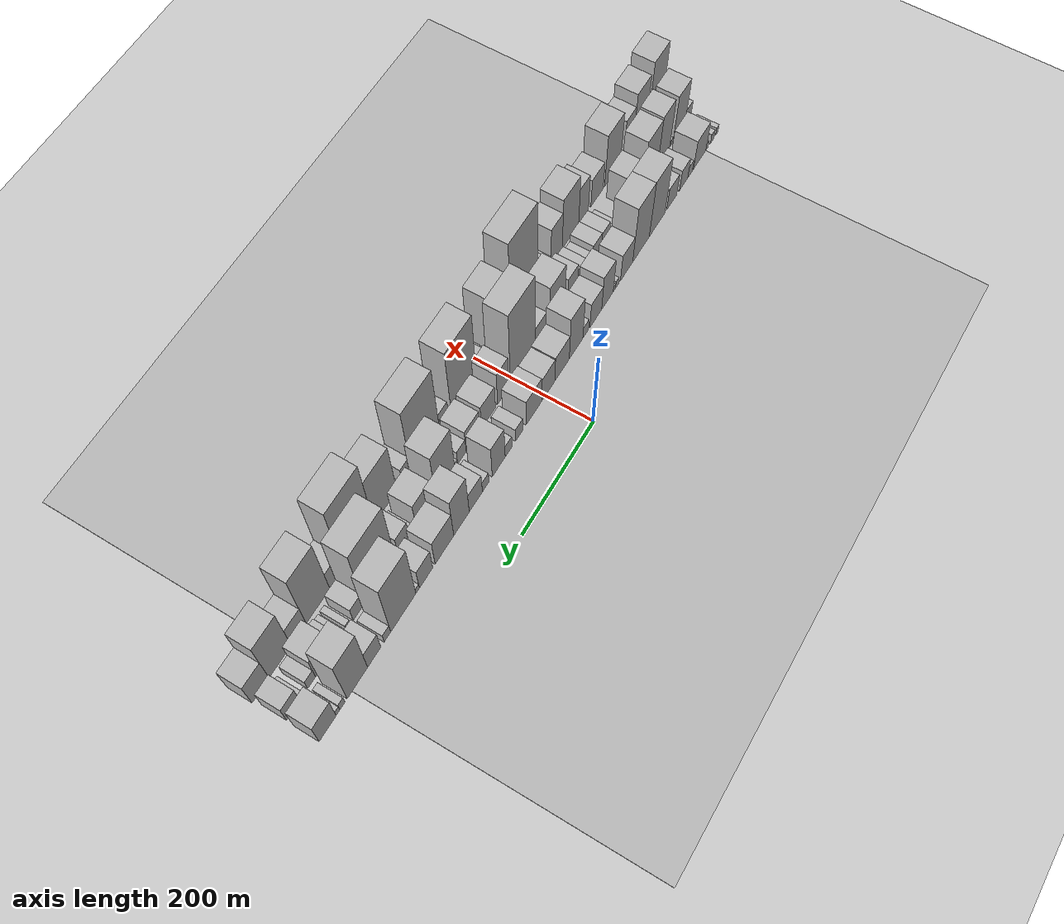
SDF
<?xml version="1.0" encoding="utf-8"?>

<sdf version="1.6">

   <world name="default">

      <gui fullscreen="0">

         <camera name="user_camera">

            <pose>-15 0 4.57585 0 0 0</pose>

            <view_controller>orbit</view_controller>

         </camera>

      </gui>

      <scene>

         <sky>

           <clouds>

             <speed>12</speed>

           </clouds>

         </sky>

         <ambient>0.4 0.4 0.4 1</ambient>

         <background>0.7 0.7 0.7 1</background>

         <shadows>1</shadows>

      </scene>

      <gravity>0 0 -9.8066</gravity>

      <magnetic_field>6e-06 2.3e-05 -4.2e-05</magnetic_field>

      <physics default="0" name="default_physics" type="ode">

         <ode>

            <solver>

               <type>quick</type>

               <iters>10</iters>

               <sor>1.0</sor>

               <use_dynamic_moi_rescaling>0</use_dynamic_moi_rescaling>

            </solver>

            <constraints>

               <cfm>0</cfm>

               <erp>0.2</erp>

               <contact_max_correcting_vel>100</contact_max_correcting_vel>

               <contact_surface_layer>0.001</contact_surface_layer>

            </constraints>

         </ode>

         <max_step_size>0.004</max_step_size>

         <real_time_factor>1</real_time_factor>

         <real_time_update_rate>250</real_time_update_rate>

      </physics>

      <light name="sun" type="directional">

         <cast_shadows>1</cast_shadows>

         <pose>0 0 10 0 0 0</pose>

         <diffuse>0.8 0.8 0.8 1</diffuse>

         <specular>0.2 0.2 0.2 1</specular>

         <attenuation>

            <range>1000</range>

            <constant>0.9</constant>

            <linear>0.01</linear>

            <quadratic>0.001</quadratic>

         </attenuation>

         <direction>-0.5 0.1 -0.9</direction>

      </light>

      <include>

         <name>ground_plane_1</name>

         <uri>model://HANNAS_ground_plane</uri>

         <pose>0 0 0  0 0 0</pose>

      </include>

      <include>

         <name>ground_plane_2</name>

         <uri>model://HANNAS_ground_plane</uri>

         <pose>100 0 0  0 0 0</pose>

      </include>

      <model name="building_1">

         <static>1</static>

         <pose frame="">100.0000 -536.7540 0 0.000000 0.000000 0.000000</pose>

         <link name="link">

            <pose frame="">0 0 10.50 0 0 0</pose>

            <collision name="collision">

               <geometry>

                  <box>

                     <size>40.0000 8.4920 21.0000</size>

                  </box>

               </geometry>

               <max_contacts>10</max_contacts>

               <surface>

                  <contact>

                     <ode/>

                  </contact>

                  <bounce/>

                  <friction>

                     <torsional>

                        <ode/>

                     </torsional>

                     <ode/>

                  </friction>

               </surface>

            </collision>

            <visual name="visual">

               <cast_shadows>0</cast_shadows>

               <geometry>

                  <box>

                     <size>40.0000 8.4920 21.0000</size>

                  </box>

               </geometry>

               <material>

                  <script>

                     <uri>model://HANNAS_wall/materials/scripts</uri>

                     <uri>model://HANNAS_wall/materials/textures</uri>

                     <name>vrc/HANNAS_wall</name>

                  </script>

               </material>

            </visual>

            <self_collide>0</self_collide>

            <enable_wind>0</enable_wind>

            <kinematic>0</kinematic>

         </link>

      </model>

      <model name="building_2">

         <static>1</static>

         <pose frame="">100.0000 -520.8953 0 0.000000 0.000000 0.000000</pose>

         <link name="link">

            <pose frame="">0 0 12.00 0 0 0</pose>

            <collision name="collision">

               <geometry>

                  <box>

                     <size>40.0000 11.2253 24.0000</size>

                  </box>

               </geometry>

               <max_contacts>10</max_contacts>

               <surface>

                  <contact>

                     <ode/>

                  </contact>

                  <bounce/>

                  <friction>

                     <torsional>

                        <ode/>

                     </torsional>

                     <ode/>

                  </friction>

               </surface>

            </collision>

            <visual name="visual">

               <cast_shadows>0</cast_shadows>

               <geometry>

                  <box>

                     <size>40.0000 11.2253 24.0000</size>

                  </box>

               </geometry>

               <material>

                  <script>

                     <uri>model://HANNAS_wall/materials/scripts</uri>

                     <uri>model://HANNAS_wall/materials/textures</uri>

                     <name>vrc/HANNAS_wall</name>

                  </script>

               </material>

            </visual>

            <self_collide>0</self_collide>

            <enable_wind>0</enable_wind>

            <kinematic>0</kinematic>

         </link>

      </model>

      <model name="building_3">

         <static>1</static>

         <pose frame="">100.0000 -503.1927 0 0.000000 0.000000 0.000000</pose>

         <link name="link">

            <pose frame="">0 0 9.00 0 0 0</pose>

            <collision name="collision">

               <geometry>

                  <box>

                     <size>40.0000 8.1800 18.0000</size>

                  </box>

               </geometry>

               <max_contacts>10</max_contacts>

               <surface>

                  <contact>

                     <ode/>

                  </contact>

                  <bounce/>

                  <friction>

                     <torsional>

                        <ode/>

                     </torsional>

                     <ode/>

                  </friction>

               </surface>

            </collision>

            <visual name="visual">

               <cast_shadows>0</cast_shadows>

               <geometry>

                  <box>

                     <size>40.0000 8.1800 18.0000</size>

                  </box>

               </geometry>

               <material>

                  <script>

                     <uri>model://HANNAS_wall/materials/scripts</uri>

                     <uri>model://HANNAS_wall/materials/textures</uri>

                     <name>vrc/HANNAS_wall</name>

                  </script>

               </material>

            </visual>

            <self_collide>0</self_collide>

            <enable_wind>0</enable_wind>

            <kinematic>0</kinematic>

         </link>

      </model>

      <model name="building_4">

         <static>1</static>

         <pose frame="">100.0000 -478.0541 0 0.000000 0.000000 0.000000</pose>

         <link name="link">

            <pose frame="">0 0 37.50 0 0 0</pose>

            <collision name="collision">

               <geometry>

                  <box>

                     <size>40.0000 42.0971 75.0000</size>

                  </box>

               </geometry>

               <max_contacts>10</max_contacts>

               <surface>

                  <contact>

                     <ode/>

                  </contact>

                  <bounce/>

                  <friction>

                     <torsional>

                        <ode/>

                     </torsional>

                     <ode/>

                  </friction>

               </surface>

            </collision>

            <visual name="visual">

               <cast_shadows>0</cast_shadows>

               <geometry>

                  <box>

                     <size>40.0000 42.0971 75.0000</size>

                  </box>

               </geometry>

               <material>

                  <script>

                     <uri>model://HANNAS_wall/materials/scripts</uri>

                     <uri>model://HANNAS_wall/materials/textures</uri>

                     <name>vrc/HANNAS_wall</name>

                  </script>

               </material>

            </visual>

            <self_collide>0</self_collide>

            <enable_wind>0</enable_wind>

            <kinematic>0</kinematic>

         </link>

      </model>

      <model name="building_5">

         <static>1</static>

         <pose frame="">100.0000 -446.2082 0 0.000000 0.000000 0.000000</pose>

         <link name="link">

            <pose frame="">0 0 15.00 0 0 0</pose>

            <collision name="collision">

               <geometry>

                  <box>

                     <size>40.0000 15.5946 30.0000</size>

                  </box>

               </geometry>

               <max_contacts>10</max_contacts>

               <surface>

                  <contact>

                     <ode/>

                  </contact>

                  <bounce/>

                  <friction>

                     <torsional>

                        <ode/>

                     </torsional>

                     <ode/>

                  </friction>

               </surface>

            </collision>

            <visual name="visual">

               <cast_shadows>0</cast_shadows>

               <geometry>

                  <box>

                     <size>40.0000 15.5946 30.0000</size>

                  </box>

               </geometry>

               <material>

                  <script>

                     <uri>model://HANNAS_wall/materials/scripts</uri>

                     <uri>model://HANNAS_wall/materials/textures</uri>

                     <name>vrc/HANNAS_wall</name>

                  </script>

               </material>

            </visual>

            <self_collide>0</self_collide>

            <enable_wind>0</enable_wind>

            <kinematic>0</kinematic>

         </link>

      </model>

      <model name="building_6">

         <static>1</static>

         <pose frame="">100.0000 -424.6408 0 0.000000 0.000000 0.000000</pose>

         <link name="link">

            <pose frame="">0 0 27.00 0 0 0</pose>

            <collision name="collision">

               <geometry>

                  <box>

                     <size>40.0000 27.5401 54.0000</size>

                  </box>

               </geometry>

               <max_contacts>10</max_contacts>

               <surface>

                  <contact>

                     <ode/>

                  </contact>

                  <bounce/>

                  <friction>

                     <torsional>

                        <ode/>

                     </torsional>

                     <ode/>

                  </friction>

               </surface>

            </collision>

            <visual name="visual">

               <cast_shadows>0</cast_shadows>

               <geometry>

                  <box>

                     <size>40.0000 27.5401 54.0000</size>

                  </box>

               </geometry>

               <material>

                  <script>

                     <uri>model://HANNAS_wall/materials/scripts</uri>

                     <uri>model://HANNAS_wall/materials/textures</uri>

                     <name>vrc/HANNAS_wall</name>

                  </script>

               </material>

            </visual>

            <self_collide>0</self_collide>

            <enable_wind>0</enable_wind>

            <kinematic>0</kinematic>

         </link>

      </model>

      <model name="building_7">

         <static>1</static>

         <pose frame="">100.0000 -385.5654 0 0.000000 0.000000 0.000000</pose>

         <link name="link">

            <pose frame="">0 0 28.50 0 0 0</pose>

            <collision name="collision">

               <geometry>

                  <box>

                     <size>40.0000 32.6109 57.0000</size>

                  </box>

               </geometry>

               <max_contacts>10</max_contacts>

               <surface>

                  <contact>

                     <ode/>

                  </contact>

                  <bounce/>

                  <friction>

                     <torsional>

                        <ode/>

                     </torsional>

                     <ode/>

                  </friction>

               </surface>

            </collision>

            <visual name="visual">

               <cast_shadows>0</cast_shadows>

               <geometry>

                  <box>

                     <size>40.0000 32.6109 57.0000</size>

                  </box>

               </geometry>

               <material>

                  <script>

                     <uri>model://HANNAS_wall/materials/scripts</uri>

                     <uri>model://HANNAS_wall/materials/textures</uri>

                     <name>vrc/HANNAS_wall</name>

                  </script>

               </material>

            </visual>

            <self_collide>0</self_collide>

            <enable_wind>0</enable_wind>

            <kinematic>0</kinematic>

         </link>

      </model>

      <model name="building_8">

         <static>1</static>

         <pose frame="">100.0000 -338.2267 0 0.000000 0.000000 0.000000</pose>

         <link name="link">

            <pose frame="">0 0 73.50 0 0 0</pose>

            <collision name="collision">

               <geometry>

                  <box>

                     <size>40.0000 50.0665 147.0000</size>

                  </box>

               </geometry>

               <max_contacts>10</max_contacts>

               <surface>

                  <contact>

                     <ode/>

                  </contact>

                  <bounce/>

                  <friction>

                     <torsional>

                        <ode/>

                     </torsional>

                     <ode/>

                  </friction>

               </surface>

            </collision>

            <visual name="visual">

               <cast_shadows>0</cast_shadows>

               <geometry>

                  <box>

                     <size>40.0000 50.0665 147.0000</size>

                  </box>

               </geometry>

               <material>

                  <script>

                     <uri>model://HANNAS_wall/materials/scripts</uri>

                     <uri>model://HANNAS_wall/materials/textures</uri>

                     <name>vrc/HANNAS_wall</name>

                  </script>

               </material>

            </visual>

            <self_collide>0</self_collide>

            <enable_wind>0</enable_wind>

            <kinematic>0</kinematic>

         </link>

      </model>

      <model name="building_9">

         <static>1</static>

         <pose frame="">100.0000 -286.8688 0 0.000000 0.000000 0.000000</pose>

         <link name="link">

            <pose frame="">0 0 73.50 0 0 0</pose>

            <collision name="collision">

               <geometry>

                  <box>

                     <size>40.0000 52.6494 147.0000</size>

                  </box>

               </geometry>

               <max_contacts>10</max_contacts>

               <surface>

                  <contact>

                     <ode/>

                  </contact>

                  <bounce/>

                  <friction>

                     <torsional>

                        <ode/>

                     </torsional>

                     <ode/>

                  </friction>

               </surface>

            </collision>

            <visual name="visual">

               <cast_shadows>0</cast_shadows>

               <geometry>

                  <box>

                     <size>40.0000 52.6494 147.0000</size>

                  </box>

               </geometry>

               <material>

                  <script>

                     <uri>model://HANNAS_wall/materials/scripts</uri>

                     <uri>model://HANNAS_wall/materials/textures</uri>

                     <name>vrc/HANNAS_wall</name>

                  </script>

               </material>

            </visual>

            <self_collide>0</self_collide>

            <enable_wind>0</enable_wind>

            <kinematic>0</kinematic>

         </link>

      </model>

      <model name="building_10">

         <static>1</static>

         <pose frame="">100.0000 -241.4833 0 0.000000 0.000000 0.000000</pose>

         <link name="link">

            <pose frame="">0 0 36.00 0 0 0</pose>

            <collision name="collision">

               <geometry>

                  <box>

                     <size>40.0000 38.1215 72.0000</size>

                  </box>

               </geometry>

               <max_contacts>10</max_contacts>

               <surface>

                  <contact>

                     <ode/>

                  </contact>

                  <bounce/>

                  <friction>

                     <torsional>

                        <ode/>

                     </torsional>

                     <ode/>

                  </friction>

               </surface>

            </collision>

            <visual name="visual">

               <cast_shadows>0</cast_shadows>

               <geometry>

                  <box>

                     <size>40.0000 38.1215 72.0000</size>

                  </box>

               </geometry>

               <material>

                  <script>

                     <uri>model://HANNAS_wall/materials/scripts</uri>

                     <uri>model://HANNAS_wall/materials/textures</uri>

                     <name>vrc/HANNAS_wall</name>

                  </script>

               </material>

            </visual>

            <self_collide>0</self_collide>

            <enable_wind>0</enable_wind>

            <kinematic>0</kinematic>

         </link>

      </model>

      <model name="building_11">

         <static>1</static>

         <pose frame="">100.0000 -211.9873 0 0.000000 0.000000 0.000000</pose>

         <link name="link">

            <pose frame="">0 0 10.50 0 0 0</pose>

            <collision name="collision">

               <geometry>

                  <box>

                     <size>40.0000 8.8707 21.0000</size>

                  </box>

               </geometry>

               <max_contacts>10</max_contacts>

               <surface>

                  <contact>

                     <ode/>

                  </contact>

                  <bounce/>

                  <friction>

                     <torsional>

                        <ode/>

                     </torsional>

                     <ode/>

                  </friction>

               </surface>

            </collision>

            <visual name="visual">

               <cast_shadows>0</cast_shadows>

               <geometry>

                  <box>

                     <size>40.0000 8.8707 21.0000</size>

                  </box>

               </geometry>

               <material>

                  <script>

                     <uri>model://HANNAS_wall/materials/scripts</uri>

                     <uri>model://HANNAS_wall/materials/textures</uri>

                     <name>vrc/HANNAS_wall</name>

                  </script>

               </material>

            </visual>

            <self_collide>0</self_collide>

            <enable_wind>0</enable_wind>

            <kinematic>0</kinematic>

         </link>

      </model>

      <model name="building_12">

         <static>1</static>

         <pose frame="">100.0000 -203.8857 0 0.000000 0.000000 0.000000</pose>

         <link name="link">

            <pose frame="">0 0 7.50 0 0 0</pose>

            <collision name="collision">

               <geometry>

                  <box>

                     <size>40.0000 7.3324 15.0000</size>

                  </box>

               </geometry>

               <max_contacts>10</max_contacts>

               <surface>

                  <contact>

                     <ode/>

                  </contact>

                  <bounce/>

                  <friction>

                     <torsional>

                        <ode/>

                     </torsional>

                     <ode/>

                  </friction>

               </surface>

            </collision>

            <visual name="visual">

               <cast_shadows>0</cast_shadows>

               <geometry>

                  <box>

                     <size>40.0000 7.3324 15.0000</size>

                  </box>

               </geometry>

               <material>

                  <script>

                     <uri>model://HANNAS_wall/materials/scripts</uri>

                     <uri>model://HANNAS_wall/materials/textures</uri>

                     <name>vrc/HANNAS_wall</name>

                  </script>

               </material>

            </visual>

            <self_collide>0</self_collide>

            <enable_wind>0</enable_wind>

            <kinematic>0</kinematic>

         </link>

      </model>

      <model name="building_13">

         <static>1</static>

         <pose frame="">100.0000 -182.5915 0 0.000000 0.000000 0.000000</pose>

         <link name="link">

            <pose frame="">0 0 46.50 0 0 0</pose>

            <collision name="collision">

               <geometry>

                  <box>

                     <size>40.0000 35.2561 93.0000</size>

                  </box>

               </geometry>

               <max_contacts>10</max_contacts>

               <surface>

                  <contact>

                     <ode/>

                  </contact>

                  <bounce/>

                  <friction>

                     <torsional>

                        <ode/>

                     </torsional>

                     <ode/>

                  </friction>

               </surface>

            </collision>

            <visual name="visual">

               <cast_shadows>0</cast_shadows>

               <geometry>

                  <box>

                     <size>40.0000 35.2561 93.0000</size>

                  </box>

               </geometry>

               <material>

                  <script>

                     <uri>model://HANNAS_wall/materials/scripts</uri>

                     <uri>model://HANNAS_wall/materials/textures</uri>

                     <name>vrc/HANNAS_wall</name>

                  </script>

               </material>

            </visual>

            <self_collide>0</self_collide>

            <enable_wind>0</enable_wind>

            <kinematic>0</kinematic>

         </link>

      </model>

      <model name="building_14">

         <static>1</static>

         <pose frame="">100.0000 -147.2904 0 0.000000 0.000000 0.000000</pose>

         <link name="link">

            <pose frame="">0 0 34.50 0 0 0</pose>

            <collision name="collision">

               <geometry>

                  <box>

                     <size>40.0000 35.3460 69.0000</size>

                  </box>

               </geometry>

               <max_contacts>10</max_contacts>

               <surface>

                  <contact>

                     <ode/>

                  </contact>

                  <bounce/>

                  <friction>

                     <torsional>

                        <ode/>

                     </torsional>

                     <ode/>

                  </friction>

               </surface>

            </collision>

            <visual name="visual">

               <cast_shadows>0</cast_shadows>

               <geometry>

                  <box>

                     <size>40.0000 35.3460 69.0000</size>

                  </box>

               </geometry>

               <material>

                  <script>

                     <uri>model://HANNAS_wall/materials/scripts</uri>

                     <uri>model://HANNAS_wall/materials/textures</uri>

                     <name>vrc/HANNAS_wall</name>

                  </script>

               </material>

            </visual>

            <self_collide>0</self_collide>

            <enable_wind>0</enable_wind>

            <kinematic>0</kinematic>

         </link>

      </model>

      <model name="building_15">

         <static>1</static>

         <pose frame="">100.0000 -117.1460 0 0.000000 0.000000 0.000000</pose>

         <link name="link">

            <pose frame="">0 0 16.50 0 0 0</pose>

            <collision name="collision">

               <geometry>

                  <box>

                     <size>40.0000 16.9429 33.0000</size>

                  </box>

               </geometry>

               <max_contacts>10</max_contacts>

               <surface>

                  <contact>

                     <ode/>

                  </contact>

                  <bounce/>

                  <friction>

                     <torsional>

                        <ode/>

                     </torsional>

                     <ode/>

                  </friction>

               </surface>

            </collision>

            <visual name="visual">

               <cast_shadows>0</cast_shadows>

               <geometry>

                  <box>

                     <size>40.0000 16.9429 33.0000</size>

                  </box>

               </geometry>

               <material>

                  <script>

                     <uri>model://HANNAS_wall/materials/scripts</uri>

                     <uri>model://HANNAS_wall/materials/textures</uri>

                     <name>vrc/HANNAS_wall</name>

                  </script>

               </material>

            </visual>

            <self_collide>0</self_collide>

            <enable_wind>0</enable_wind>

            <kinematic>0</kinematic>

         </link>

      </model>

      <model name="building_16">

         <static>1</static>

         <pose frame="">100.0000 -88.7825 0 0.000000 0.000000 0.000000</pose>

         <link name="link">

            <pose frame="">0 0 60.00 0 0 0</pose>

            <collision name="collision">

               <geometry>

                  <box>

                     <size>40.0000 39.7841 120.0000</size>

                  </box>

               </geometry>

               <max_contacts>10</max_contacts>

               <surface>

                  <contact>

                     <ode/>

                  </contact>

                  <bounce/>

                  <friction>

                     <torsional>

                        <ode/>

                     </torsional>

                     <ode/>

                  </friction>

               </surface>

            </collision>

            <visual name="visual">

               <cast_shadows>0</cast_shadows>

               <geometry>

                  <box>

                     <size>40.0000 39.7841 120.0000</size>

                  </box>

               </geometry>

               <material>

                  <script>

                     <uri>model://HANNAS_wall/materials/scripts</uri>

                     <uri>model://HANNAS_wall/materials/textures</uri>

                     <name>vrc/HANNAS_wall</name>

                  </script>

               </material>

            </visual>

            <self_collide>0</self_collide>

            <enable_wind>0</enable_wind>

            <kinematic>0</kinematic>

         </link>

      </model>

      <model name="building_17">

         <static>1</static>

         <pose frame="">100.0000 -48.1109 0 0.000000 0.000000 0.000000</pose>

         <link name="link">

            <pose frame="">0 0 36.00 0 0 0</pose>

            <collision name="collision">

               <geometry>

                  <box>

                     <size>40.0000 41.5592 72.0000</size>

                  </box>

               </geometry>

               <max_contacts>10</max_contacts>

               <surface>

                  <contact>

                     <ode/>

                  </contact>

                  <bounce/>

                  <friction>

                     <torsional>

                        <ode/>

                     </torsional>

                     <ode/>

                  </friction>

               </surface>

            </collision>

            <visual name="visual">

               <cast_shadows>0</cast_shadows>

               <geometry>

                  <box>

                     <size>40.0000 41.5592 72.0000</size>

                  </box>

               </geometry>

               <material>

                  <script>

                     <uri>model://HANNAS_wall/materials/scripts</uri>

                     <uri>model://HANNAS_wall/materials/textures</uri>

                     <name>vrc/HANNAS_wall</name>

                  </script>

               </material>

            </visual>

            <self_collide>0</self_collide>

            <enable_wind>0</enable_wind>

            <kinematic>0</kinematic>

         </link>

      </model>

      <model name="building_18">

         <static>1</static>

         <pose frame="">100.0000 -8.3283 0 0.000000 0.000000 0.000000</pose>

         <link name="link">

            <pose frame="">0 0 34.50 0 0 0</pose>

            <collision name="collision">

               <geometry>

                  <box>

                     <size>40.0000 38.0060 69.0000</size>

                  </box>

               </geometry>

               <max_contacts>10</max_contacts>

               <surface>

                  <contact>

                     <ode/>

                  </contact>

                  <bounce/>

                  <friction>

                     <torsional>

                        <ode/>

                     </torsional>

                     <ode/>

                  </friction>

               </surface>

            </collision>

            <visual name="visual">

               <cast_shadows>0</cast_shadows>

               <geometry>

                  <box>

                     <size>40.0000 38.0060 69.0000</size>

                  </box>

               </geometry>

               <material>

                  <script>

                     <uri>model://HANNAS_wall/materials/scripts</uri>

                     <uri>model://HANNAS_wall/materials/textures</uri>

                     <name>vrc/HANNAS_wall</name>

                  </script>

               </material>

            </visual>

            <self_collide>0</self_collide>

            <enable_wind>0</enable_wind>

            <kinematic>0</kinematic>

         </link>

      </model>

      <model name="building_19">

         <static>1</static>

         <pose frame="">100.0000 32.2616 0 0.000000 0.000000 0.000000</pose>

         <link name="link">

            <pose frame="">0 0 37.50 0 0 0</pose>

            <collision name="collision">

               <geometry>

                  <box>

                     <size>40.0000 43.1738 75.0000</size>

                  </box>

               </geometry>

               <max_contacts>10</max_contacts>

               <surface>

                  <contact>

                     <ode/>

                  </contact>

                  <bounce/>

                  <friction>

                     <torsional>

                        <ode/>

                     </torsional>

                     <ode/>

                  </friction>

               </surface>

            </collision>

            <visual name="visual">

               <cast_shadows>0</cast_shadows>

               <geometry>

                  <box>

                     <size>40.0000 43.1738 75.0000</size>

                  </box>

               </geometry>

               <material>

                  <script>

                     <uri>model://HANNAS_wall/materials/scripts</uri>

                     <uri>model://HANNAS_wall/materials/textures</uri>

                     <name>vrc/HANNAS_wall</name>

                  </script>

               </material>

            </visual>

            <self_collide>0</self_collide>

            <enable_wind>0</enable_wind>

            <kinematic>0</kinematic>

         </link>

      </model>

      <model name="building_20">

         <static>1</static>

         <pose frame="">100.0000 73.1810 0 0.000000 0.000000 0.000000</pose>

         <link name="link">

            <pose frame="">0 0 19.50 0 0 0</pose>

            <collision name="collision">

               <geometry>

                  <box>

                     <size>40.0000 20.6649 39.0000</size>

                  </box>

               </geometry>

               <max_contacts>10</max_contacts>

               <surface>

                  <contact>

                     <ode/>

                  </contact>

                  <bounce/>

                  <friction>

                     <torsional>

                        <ode/>

                     </torsional>

                     <ode/>

                  </friction>

               </surface>

            </collision>

            <visual name="visual">

               <cast_shadows>0</cast_shadows>

               <geometry>

                  <box>

                     <size>40.0000 20.6649 39.0000</size>

                  </box>

               </geometry>

               <material>

                  <script>

                     <uri>model://HANNAS_wall/materials/scripts</uri>

                     <uri>model://HANNAS_wall/materials/textures</uri>

                     <name>vrc/HANNAS_wall</name>

                  </script>

               </material>

            </visual>

            <self_collide>0</self_collide>

            <enable_wind>0</enable_wind>

            <kinematic>0</kinematic>

         </link>

      </model>

      <model name="building_21">

         <static>1</static>

         <pose frame="">100.0000 102.8595 0 0.000000 0.000000 0.000000</pose>

         <link name="link">

            <pose frame="">0 0 18.00 0 0 0</pose>

            <collision name="collision">

               <geometry>

                  <box>

                     <size>40.0000 18.6922 36.0000</size>

                  </box>

               </geometry>

               <max_contacts>10</max_contacts>

               <surface>

                  <contact>

                     <ode/>

                  </contact>

                  <bounce/>

                  <friction>

                     <torsional>

                        <ode/>

                     </torsional>

                     <ode/>

                  </friction>

               </surface>

            </collision>

            <visual name="visual">

               <cast_shadows>0</cast_shadows>

               <geometry>

                  <box>

                     <size>40.0000 18.6922 36.0000</size>

                  </box>

               </geometry>

               <material>

                  <script>

                     <uri>model://HANNAS_wall/materials/scripts</uri>

                     <uri>model://HANNAS_wall/materials/textures</uri>

                     <name>vrc/HANNAS_wall</name>

                  </script>

               </material>

            </visual>

            <self_collide>0</self_collide>

            <enable_wind>0</enable_wind>

            <kinematic>0</kinematic>

         </link>

      </model>

      <model name="building_22">

         <static>1</static>

         <pose frame="">100.0000 129.7020 0 0.000000 0.000000 0.000000</pose>

         <link name="link">

            <pose frame="">0 0 48.00 0 0 0</pose>

            <collision name="collision">

               <geometry>

                  <box>

                     <size>40.0000 34.9927 96.0000</size>

                  </box>

               </geometry>

               <max_contacts>10</max_contacts>

               <surface>

                  <contact>

                     <ode/>

                  </contact>

                  <bounce/>

                  <friction>

                     <torsional>

                        <ode/>

                     </torsional>

                     <ode/>

                  </friction>

               </surface>

            </collision>

            <visual name="visual">

               <cast_shadows>0</cast_shadows>

               <geometry>

                  <box>

                     <size>40.0000 34.9927 96.0000</size>

                  </box>

               </geometry>

               <material>

                  <script>

                     <uri>model://HANNAS_wall/materials/scripts</uri>

                     <uri>model://HANNAS_wall/materials/textures</uri>

                     <name>vrc/HANNAS_wall</name>

                  </script>

               </material>

            </visual>

            <self_collide>0</self_collide>

            <enable_wind>0</enable_wind>

            <kinematic>0</kinematic>

         </link>

      </model>

      <model name="building_23">

         <static>1</static>

         <pose frame="">100.0000 164.9879 0 0.000000 0.000000 0.000000</pose>

         <link name="link">

            <pose frame="">0 0 16.50 0 0 0</pose>

            <collision name="collision">

               <geometry>

                  <box>

                     <size>40.0000 17.5790 33.0000</size>

                  </box>

               </geometry>

               <max_contacts>10</max_contacts>

               <surface>

                  <contact>

                     <ode/>

                  </contact>

                  <bounce/>

                  <friction>

                     <torsional>

                        <ode/>

                     </torsional>

                     <ode/>

                  </friction>

               </surface>

            </collision>

            <visual name="visual">

               <cast_shadows>0</cast_shadows>

               <geometry>

                  <box>

                     <size>40.0000 17.5790 33.0000</size>

                  </box>

               </geometry>

               <material>

                  <script>

                     <uri>model://HANNAS_wall/materials/scripts</uri>

                     <uri>model://HANNAS_wall/materials/textures</uri>

                     <name>vrc/HANNAS_wall</name>

                  </script>

               </material>

            </visual>

            <self_collide>0</self_collide>

            <enable_wind>0</enable_wind>

            <kinematic>0</kinematic>

         </link>

      </model>

      <model name="building_24">

         <static>1</static>

         <pose frame="">100.0000 191.1892 0 0.000000 0.000000 0.000000</pose>

         <link name="link">

            <pose frame="">0 0 30.00 0 0 0</pose>

            <collision name="collision">

               <geometry>

                  <box>

                     <size>40.0000 34.8237 60.0000</size>

                  </box>

               </geometry>

               <max_contacts>10</max_contacts>

               <surface>

                  <contact>

                     <ode/>

                  </contact>

                  <bounce/>

                  <friction>

                     <torsional>

                        <ode/>

                     </torsional>

                     <ode/>

                  </friction>

               </surface>

            </collision>

            <visual name="visual">

               <cast_shadows>0</cast_shadows>

               <geometry>

                  <box>

                     <size>40.0000 34.8237 60.0000</size>

                  </box>

               </geometry>

               <material>

                  <script>

                     <uri>model://HANNAS_wall/materials/scripts</uri>

                     <uri>model://HANNAS_wall/materials/textures</uri>

                     <name>vrc/HANNAS_wall</name>

                  </script>

               </material>

            </visual>

            <self_collide>0</self_collide>

            <enable_wind>0</enable_wind>

            <kinematic>0</kinematic>

         </link>

      </model>

      <model name="building_25">

         <static>1</static>

         <pose frame="">100.0000 228.8745 0 0.000000 0.000000 0.000000</pose>

         <link name="link">

            <pose frame="">0 0 61.50 0 0 0</pose>

            <collision name="collision">

               <geometry>

                  <box>

                     <size>40.0000 40.5469 123.0000</size>

                  </box>

               </geometry>

               <max_contacts>10</max_contacts>

               <surface>

                  <contact>

                     <ode/>

                  </contact>

                  <bounce/>

                  <friction>

                     <torsional>

                        <ode/>

                     </torsional>

                     <ode/>

                  </friction>

               </surface>

            </collision>

            <visual name="visual">

               <cast_shadows>0</cast_shadows>

               <geometry>

                  <box>

                     <size>40.0000 40.5469 123.0000</size>

                  </box>

               </geometry>

               <material>

                  <script>

                     <uri>model://HANNAS_wall/materials/scripts</uri>

                     <uri>model://HANNAS_wall/materials/textures</uri>

                     <name>vrc/HANNAS_wall</name>

                  </script>

               </material>

            </visual>

            <self_collide>0</self_collide>

            <enable_wind>0</enable_wind>

            <kinematic>0</kinematic>

         </link>

      </model>

      <model name="building_26">

         <static>1</static>

         <pose frame="">100.0000 273.0367 0 0.000000 0.000000 0.000000</pose>

         <link name="link">

            <pose frame="">0 0 40.50 0 0 0</pose>

            <collision name="collision">

               <geometry>

                  <box>

                     <size>40.0000 47.7774 81.0000</size>

                  </box>

               </geometry>

               <max_contacts>10</max_contacts>

               <surface>

                  <contact>

                     <ode/>

                  </contact>

                  <bounce/>

                  <friction>

                     <torsional>

                        <ode/>

                     </torsional>

                     <ode/>

                  </friction>

               </surface>

            </collision>

            <visual name="visual">

               <cast_shadows>0</cast_shadows>

               <geometry>

                  <box>

                     <size>40.0000 47.7774 81.0000</size>

                  </box>

               </geometry>

               <material>

                  <script>

                     <uri>model://HANNAS_wall/materials/scripts</uri>

                     <uri>model://HANNAS_wall/materials/textures</uri>

                     <name>vrc/HANNAS_wall</name>

                  </script>

               </material>

            </visual>

            <self_collide>0</self_collide>

            <enable_wind>0</enable_wind>

            <kinematic>0</kinematic>

         </link>

      </model>

      <model name="building_27">

         <static>1</static>

         <pose frame="">100.0000 319.7425 0 0.000000 0.000000 0.000000</pose>

         <link name="link">

            <pose frame="">0 0 33.00 0 0 0</pose>

            <collision name="collision">

               <geometry>

                  <box>

                     <size>40.0000 33.6341 66.0000</size>

                  </box>

               </geometry>

               <max_contacts>10</max_contacts>

               <surface>

                  <contact>

                     <ode/>

                  </contact>

                  <bounce/>

                  <friction>

                     <torsional>

                        <ode/>

                     </torsional>

                     <ode/>

                  </friction>

               </surface>

            </collision>

            <visual name="visual">

               <cast_shadows>0</cast_shadows>

               <geometry>

                  <box>

                     <size>40.0000 33.6341 66.0000</size>

                  </box>

               </geometry>

               <material>

                  <script>

                     <uri>model://HANNAS_wall/materials/scripts</uri>

                     <uri>model://HANNAS_wall/materials/textures</uri>

                     <name>vrc/HANNAS_wall</name>

                  </script>

               </material>

            </visual>

            <self_collide>0</self_collide>

            <enable_wind>0</enable_wind>

            <kinematic>0</kinematic>

         </link>

      </model>

      <model name="building_28">

         <static>1</static>

         <pose frame="">100.0000 341.0552 0 0.000000 0.000000 0.000000</pose>

         <link name="link">

            <pose frame="">0 0 9.00 0 0 0</pose>

            <collision name="collision">

               <geometry>

                  <box>

                     <size>40.0000 8.9914 18.0000</size>

                  </box>

               </geometry>

               <max_contacts>10</max_contacts>

               <surface>

                  <contact>

                     <ode/>

                  </contact>

                  <bounce/>

                  <friction>

                     <torsional>

                        <ode/>

                     </torsional>

                     <ode/>

                  </friction>

               </surface>

            </collision>

            <visual name="visual">

               <cast_shadows>0</cast_shadows>

               <geometry>

                  <box>

                     <size>40.0000 8.9914 18.0000</size>

                  </box>

               </geometry>

               <material>

                  <script>

                     <uri>model://HANNAS_wall/materials/scripts</uri>

                     <uri>model://HANNAS_wall/materials/textures</uri>

                     <name>vrc/HANNAS_wall</name>

                  </script>

               </material>

            </visual>

            <self_collide>0</self_collide>

            <enable_wind>0</enable_wind>

            <kinematic>0</kinematic>

         </link>

      </model>

      <model name="building_29">

         <static>1</static>

         <pose frame="">100.0000 376.5766 0 0.000000 0.000000 0.000000</pose>

         <link name="link">

            <pose frame="">0 0 87.00 0 0 0</pose>

            <collision name="collision">

               <geometry>

                  <box>

                     <size>40.0000 62.0514 174.0000</size>

                  </box>

               </geometry>

               <max_contacts>10</max_contacts>

               <surface>

                  <contact>

                     <ode/>

                  </contact>

                  <bounce/>

                  <friction>

                     <torsional>

                        <ode/>

                     </torsional>

                     <ode/>

                  </friction>

               </surface>

            </collision>

            <visual name="visual">

               <cast_shadows>0</cast_shadows>

               <geometry>

                  <box>

                     <size>40.0000 62.0514 174.0000</size>

                  </box>

               </geometry>

               <material>

                  <script>

                     <uri>model://HANNAS_wall/materials/scripts</uri>

                     <uri>model://HANNAS_wall/materials/textures</uri>

                     <name>vrc/HANNAS_wall</name>

                  </script>

               </material>

            </visual>

            <self_collide>0</self_collide>

            <enable_wind>0</enable_wind>

            <kinematic>0</kinematic>

         </link>

      </model>

      <model name="building_30">

         <static>1</static>

         <pose frame="">100.0000 415.5461 0 0.000000 0.000000 0.000000</pose>

         <link name="link">

            <pose frame="">0 0 15.00 0 0 0</pose>

            <collision name="collision">

               <geometry>

                  <box>

                     <size>40.0000 15.8877 30.0000</size>

                  </box>

               </geometry>

               <max_contacts>10</max_contacts>

               <surface>

                  <contact>

                     <ode/>

                  </contact>

                  <bounce/>

                  <friction>

                     <torsional>

                        <ode/>

                     </torsional>

                     <ode/>

                  </friction>

               </surface>

            </collision>

            <visual name="visual">

               <cast_shadows>0</cast_shadows>

               <geometry>

                  <box>

                     <size>40.0000 15.8877 30.0000</size>

                  </box>

               </geometry>

               <material>

                  <script>

                     <uri>model://HANNAS_wall/materials/scripts</uri>

                     <uri>model://HANNAS_wall/materials/textures</uri>

                     <name>vrc/HANNAS_wall</name>

                  </script>

               </material>

            </visual>

            <self_collide>0</self_collide>

            <enable_wind>0</enable_wind>

            <kinematic>0</kinematic>

         </link>

      </model>

      <model name="building_31">

         <static>1</static>

         <pose frame="">100.0000 447.3565 0 0.000000 0.000000 0.000000</pose>

         <link name="link">

            <pose frame="">0 0 30.00 0 0 0</pose>

            <collision name="collision">

               <geometry>

                  <box>

                     <size>40.0000 31.7331 60.0000</size>

                  </box>

               </geometry>

               <max_contacts>10</max_contacts>

               <surface>

                  <contact>

                     <ode/>

                  </contact>

                  <bounce/>

                  <friction>

                     <torsional>

                        <ode/>

                     </torsional>

                     <ode/>

                  </friction>

               </surface>

            </collision>

            <visual name="visual">

               <cast_shadows>0</cast_shadows>

               <geometry>

                  <box>

                     <size>40.0000 31.7331 60.0000</size>

                  </box>

               </geometry>

               <material>

                  <script>

                     <uri>model://HANNAS_wall/materials/scripts</uri>

                     <uri>model://HANNAS_wall/materials/textures</uri>

                     <name>vrc/HANNAS_wall</name>

                  </script>

               </material>

            </visual>

            <self_collide>0</self_collide>

            <enable_wind>0</enable_wind>

            <kinematic>0</kinematic>

         </link>

      </model>

      <model name="building_32">

         <static>1</static>

         <pose frame="">100.0000 487.4718 0 0.000000 0.000000 0.000000</pose>

         <link name="link">

            <pose frame="">0 0 75.00 0 0 0</pose>

            <collision name="collision">

               <geometry>

                  <box>

                     <size>40.0000 48.4975 150.0000</size>

                  </box>

               </geometry>

               <max_contacts>10</max_contacts>

               <surface>

                  <contact>

                     <ode/>

                  </contact>

                  <bounce/>

                  <friction>

                     <torsional>

                        <ode/>

                     </torsional>

                     <ode/>

                  </friction>

               </surface>

            </collision>

            <visual name="visual">

               <cast_shadows>0</cast_shadows>

               <geometry>

                  <box>

                     <size>40.0000 48.4975 150.0000</size>

                  </box>

               </geometry>

               <material>

                  <script>

                     <uri>model://HANNAS_wall/materials/scripts</uri>

                     <uri>model://HANNAS_wall/materials/textures</uri>

                     <name>vrc/HANNAS_wall</name>

                  </script>

               </material>

            </visual>

            <self_collide>0</self_collide>

            <enable_wind>0</enable_wind>

            <kinematic>0</kinematic>

         </link>

      </model>

      <model name="building_33">

         <static>1</static>

         <pose frame="">100.0000 522.6468 0 0.000000 0.000000 0.000000</pose>

         <link name="link">

            <pose frame="">0 0 12.00 0 0 0</pose>

            <collision name="collision">

               <geometry>

                  <box>

                     <size>40.0000 11.8524 24.0000</size>

                  </box>

               </geometry>

               <max_contacts>10</max_contacts>

               <surface>

                  <contact>

                     <ode/>

                  </contact>

                  <bounce/>

                  <friction>

                     <torsional>

                        <ode/>

                     </torsional>

                     <ode/>

                  </friction>

               </surface>

            </collision>

            <visual name="visual">

               <cast_shadows>0</cast_shadows>

               <geometry>

                  <box>

                     <size>40.0000 11.8524 24.0000</size>

                  </box>

               </geometry>

               <material>

                  <script>

                     <uri>model://HANNAS_wall/materials/scripts</uri>

                     <uri>model://HANNAS_wall/materials/textures</uri>

                     <name>vrc/HANNAS_wall</name>

                  </script>

               </material>

            </visual>

            <self_collide>0</self_collide>

            <enable_wind>0</enable_wind>

            <kinematic>0</kinematic>

         </link>

      </model>

      <model name="building_34">

         <static>1</static>

         <pose frame="">100.0000 532.8101 0 0.000000 0.000000 0.000000</pose>

         <link name="link">

            <pose frame="">0 0 9.00 0 0 0</pose>

            <collision name="collision">

               <geometry>

                  <box>

                     <size>40.0000 8.4741 18.0000</size>

                  </box>

               </geometry>

               <max_contacts>10</max_contacts>

               <surface>

                  <contact>

                     <ode/>

                  </contact>

                  <bounce/>

                  <friction>

                     <torsional>

                        <ode/>

                     </torsional>

                     <ode/>

                  </friction>

               </surface>

            </collision>

            <visual name="visual">

               <cast_shadows>0</cast_shadows>

               <geometry>

                  <box>

                     <size>40.0000 8.4741 18.0000</size>

                  </box>

               </geometry>

               <material>

                  <script>

                     <uri>model://HANNAS_wall/materials/scripts</uri>

                     <uri>model://HANNAS_wall/materials/textures</uri>

                     <name>vrc/HANNAS_wall</name>

                  </script>

               </material>

            </visual>

            <self_collide>0</self_collide>

            <enable_wind>0</enable_wind>

            <kinematic>0</kinematic>

         </link>

      </model>

      <model name="building_35">

         <static>1</static>

         <pose frame="">100.0000 556.6974 0 0.000000 0.000000 0.000000</pose>

         <link name="link">

            <pose frame="">0 0 36.00 0 0 0</pose>

            <collision name="collision">

               <geometry>

                  <box>

                     <size>40.0000 39.3006 72.0000</size>

                  </box>

               </geometry>

               <max_contacts>10</max_contacts>

               <surface>

                  <contact>

                     <ode/>

                  </contact>

                  <bounce/>

                  <friction>

                     <torsional>

                        <ode/>

                     </torsional>

                     <ode/>

                  </friction>

               </surface>

            </collision>

            <visual name="visual">

               <cast_shadows>0</cast_shadows>

               <geometry>

                  <box>

                     <size>40.0000 39.3006 72.0000</size>

                  </box>

               </geometry>

               <material>

                  <script>

                     <uri>model://HANNAS_wall/materials/scripts</uri>

                     <uri>model://HANNAS_wall/materials/textures</uri>

                     <name>vrc/HANNAS_wall</name>

                  </script>

               </material>

            </visual>

            <self_collide>0</self_collide>

            <enable_wind>0</enable_wind>

            <kinematic>0</kinematic>

         </link>

      </model>

      <model name="building_36">

         <static>1</static>

         <pose frame="">152.0000 -537.2542 0 0.000000 0.000000 0.000000</pose>

         <link name="link">

            <pose frame="">0 0 19.50 0 0 0</pose>

            <collision name="collision">

               <geometry>

                  <box>

                     <size>40.0000 21.4917 39.0000</size>

                  </box>

               </geometry>

               <max_contacts>10</max_contacts>

               <surface>

                  <contact>

                     <ode/>

                  </contact>

                  <bounce/>

                  <friction>

                     <torsional>

                        <ode/>

                     </torsional>

                     <ode/>

                  </friction>

               </surface>

            </collision>

            <visual name="visual">

               <cast_shadows>0</cast_shadows>

               <geometry>

                  <box>

                     <size>40.0000 21.4917 39.0000</size>

                  </box>

               </geometry>

               <material>

                  <script>

                     <uri>model://HANNAS_wall/materials/scripts</uri>

                     <uri>model://HANNAS_wall/materials/textures</uri>

                     <name>vrc/HANNAS_wall</name>

                  </script>

               </material>

            </visual>

            <self_collide>0</self_collide>

            <enable_wind>0</enable_wind>

            <kinematic>0</kinematic>

         </link>

      </model>

      <model name="building_37">

         <static>1</static>

         <pose frame="">152.0000 -506.4666 0 0.000000 0.000000 0.000000</pose>

         <link name="link">

            <pose frame="">0 0 58.50 0 0 0</pose>

            <collision name="collision">

               <geometry>

                  <box>

                     <size>40.0000 40.0835 117.0000</size>

                  </box>

               </geometry>

               <max_contacts>10</max_contacts>

               <surface>

                  <contact>

                     <ode/>

                  </contact>

                  <bounce/>

                  <friction>

                     <torsional>

                        <ode/>

                     </torsional>

                     <ode/>

                  </friction>

               </surface>

            </collision>

            <visual name="visual">

               <cast_shadows>0</cast_shadows>

               <geometry>

                  <box>

                     <size>40.0000 40.0835 117.0000</size>

                  </box>

               </geometry>

               <material>

                  <script>

                     <uri>model://HANNAS_wall/materials/scripts</uri>

                     <uri>model://HANNAS_wall/materials/textures</uri>

                     <name>vrc/HANNAS_wall</name>

                  </script>

               </material>

            </visual>

            <self_collide>0</self_collide>

            <enable_wind>0</enable_wind>

            <kinematic>0</kinematic>

         </link>

      </model>

      <model name="building_38">

         <static>1</static>

         <pose frame="">152.0000 -482.7148 0 0.000000 0.000000 0.000000</pose>

         <link name="link">

            <pose frame="">0 0 7.50 0 0 0</pose>

            <collision name="collision">

               <geometry>

                  <box>

                     <size>40.0000 7.4202 15.0000</size>

                  </box>

               </geometry>

               <max_contacts>10</max_contacts>

               <surface>

                  <contact>

                     <ode/>

                  </contact>

                  <bounce/>

                  <friction>

                     <torsional>

                        <ode/>

                     </torsional>

                     <ode/>

                  </friction>

               </surface>

            </collision>

            <visual name="visual">

               <cast_shadows>0</cast_shadows>

               <geometry>

                  <box>

                     <size>40.0000 7.4202 15.0000</size>

                  </box>

               </geometry>

               <material>

                  <script>

                     <uri>model://HANNAS_wall/materials/scripts</uri>

                     <uri>model://HANNAS_wall/materials/textures</uri>

                     <name>vrc/HANNAS_wall</name>

                  </script>

               </material>

            </visual>

            <self_collide>0</self_collide>

            <enable_wind>0</enable_wind>

            <kinematic>0</kinematic>

         </link>

      </model>

      <model name="building_39">

         <static>1</static>

         <pose frame="">152.0000 -455.6832 0 0.000000 0.000000 0.000000</pose>

         <link name="link">

            <pose frame="">0 0 61.50 0 0 0</pose>

            <collision name="collision">

               <geometry>

                  <box>

                     <size>40.0000 38.6430 123.0000</size>

                  </box>

               </geometry>

               <max_contacts>10</max_contacts>

               <surface>

                  <contact>

                     <ode/>

                  </contact>

                  <bounce/>

                  <friction>

                     <torsional>

                        <ode/>

                     </torsional>

                     <ode/>

                  </friction>

               </surface>

            </collision>

            <visual name="visual">

               <cast_shadows>0</cast_shadows>

               <geometry>

                  <box>

                     <size>40.0000 38.6430 123.0000</size>

                  </box>

               </geometry>

               <material>

                  <script>

                     <uri>model://HANNAS_wall/materials/scripts</uri>

                     <uri>model://HANNAS_wall/materials/textures</uri>

                     <name>vrc/HANNAS_wall</name>

                  </script>

               </material>

            </visual>

            <self_collide>0</self_collide>

            <enable_wind>0</enable_wind>

            <kinematic>0</kinematic>

         </link>

      </model>

      <model name="building_40">

         <static>1</static>

         <pose frame="">152.0000 -413.0229 0 0.000000 0.000000 0.000000</pose>

         <link name="link">

            <pose frame="">0 0 58.50 0 0 0</pose>

            <collision name="collision">

               <geometry>

                  <box>

                     <size>40.0000 46.6776 117.0000</size>

                  </box>

               </geometry>

               <max_contacts>10</max_contacts>

               <surface>

                  <contact>

                     <ode/>

                  </contact>

                  <bounce/>

                  <friction>

                     <torsional>

                        <ode/>

                     </torsional>

                     <ode/>

                  </friction>

               </surface>

            </collision>

            <visual name="visual">

               <cast_shadows>0</cast_shadows>

               <geometry>

                  <box>

                     <size>40.0000 46.6776 117.0000</size>

                  </box>

               </geometry>

               <material>

                  <script>

                     <uri>model://HANNAS_wall/materials/scripts</uri>

                     <uri>model://HANNAS_wall/materials/textures</uri>

                     <name>vrc/HANNAS_wall</name>

                  </script>

               </material>

            </visual>

            <self_collide>0</self_collide>

            <enable_wind>0</enable_wind>

            <kinematic>0</kinematic>

         </link>

      </model>

      <model name="building_41">

         <static>1</static>

         <pose frame="">152.0000 -363.9254 0 0.000000 0.000000 0.000000</pose>

         <link name="link">

            <pose frame="">0 0 37.50 0 0 0</pose>

            <collision name="collision">

               <geometry>

                  <box>

                     <size>40.0000 41.5174 75.0000</size>

                  </box>

               </geometry>

               <max_contacts>10</max_contacts>

               <surface>

                  <contact>

                     <ode/>

                  </contact>

                  <bounce/>

                  <friction>

                     <torsional>

                        <ode/>

                     </torsional>

                     <ode/>

                  </friction>

               </surface>

            </collision>

            <visual name="visual">

               <cast_shadows>0</cast_shadows>

               <geometry>

                  <box>

                     <size>40.0000 41.5174 75.0000</size>

                  </box>

               </geometry>

               <material>

                  <script>

                     <uri>model://HANNAS_wall/materials/scripts</uri>

                     <uri>model://HANNAS_wall/materials/textures</uri>

                     <name>vrc/HANNAS_wall</name>

                  </script>

               </material>

            </visual>

            <self_collide>0</self_collide>

            <enable_wind>0</enable_wind>

            <kinematic>0</kinematic>

         </link>

      </model>

      <model name="building_42">

         <static>1</static>

         <pose frame="">152.0000 -299.8466 0 0.000000 0.000000 0.000000</pose>

         <link name="link">

            <pose frame="">0 0 9.00 0 0 0</pose>

            <collision name="collision">

               <geometry>

                  <box>

                     <size>40.0000 8.8800 18.0000</size>

                  </box>

               </geometry>

               <max_contacts>10</max_contacts>

               <surface>

                  <contact>

                     <ode/>

                  </contact>

                  <bounce/>

                  <friction>

                     <torsional>

                        <ode/>

                     </torsional>

                     <ode/>

                  </friction>

               </surface>

            </collision>

            <visual name="visual">

               <cast_shadows>0</cast_shadows>

               <geometry>

                  <box>

                     <size>40.0000 8.8800 18.0000</size>

                  </box>

               </geometry>

               <material>

                  <script>

                     <uri>model://HANNAS_wall/materials/scripts</uri>

                     <uri>model://HANNAS_wall/materials/textures</uri>

                     <name>vrc/HANNAS_wall</name>

                  </script>

               </material>

            </visual>

            <self_collide>0</self_collide>

            <enable_wind>0</enable_wind>

            <kinematic>0</kinematic>

         </link>

      </model>

      <model name="building_43">

         <static>1</static>

         <pose frame="">152.0000 -291.3068 0 0.000000 0.000000 0.000000</pose>

         <link name="link">

            <pose frame="">0 0 9.00 0 0 0</pose>

            <collision name="collision">

               <geometry>

                  <box>

                     <size>40.0000 8.1996 18.0000</size>

                  </box>

               </geometry>

               <max_contacts>10</max_contacts>

               <surface>

                  <contact>

                     <ode/>

                  </contact>

                  <bounce/>

                  <friction>

                     <torsional>

                        <ode/>

                     </torsional>

                     <ode/>

                  </friction>

               </surface>

            </collision>

            <visual name="visual">

               <cast_shadows>0</cast_shadows>

               <geometry>

                  <box>

                     <size>40.0000 8.1996 18.0000</size>

                  </box>

               </geometry>

               <material>

                  <script>

                     <uri>model://HANNAS_wall/materials/scripts</uri>

                     <uri>model://HANNAS_wall/materials/textures</uri>

                     <name>vrc/HANNAS_wall</name>

                  </script>

               </material>

            </visual>

            <self_collide>0</self_collide>

            <enable_wind>0</enable_wind>

            <kinematic>0</kinematic>

         </link>

      </model>

      <model name="building_44">

         <static>1</static>

         <pose frame="">152.0000 -268.6145 0 0.000000 0.000000 0.000000</pose>

         <link name="link">

            <pose frame="">0 0 22.50 0 0 0</pose>

            <collision name="collision">

               <geometry>

                  <box>

                     <size>40.0000 25.1849 45.0000</size>

                  </box>

               </geometry>

               <max_contacts>10</max_contacts>

               <surface>

                  <contact>

                     <ode/>

                  </contact>

                  <bounce/>

                  <friction>

                     <torsional>

                        <ode/>

                     </torsional>

                     <ode/>

                  </friction>

               </surface>

            </collision>

            <visual name="visual">

               <cast_shadows>0</cast_shadows>

               <geometry>

                  <box>

                     <size>40.0000 25.1849 45.0000</size>

                  </box>

               </geometry>

               <material>

                  <script>

                     <uri>model://HANNAS_wall/materials/scripts</uri>

                     <uri>model://HANNAS_wall/materials/textures</uri>

                     <name>vrc/HANNAS_wall</name>

                  </script>

               </material>

            </visual>

            <self_collide>0</self_collide>

            <enable_wind>0</enable_wind>

            <kinematic>0</kinematic>

         </link>

      </model>

      <model name="building_45">

         <static>1</static>

         <pose frame="">152.0000 -242.4878 0 0.000000 0.000000 0.000000</pose>

         <link name="link">

            <pose frame="">0 0 24.00 0 0 0</pose>

            <collision name="collision">

               <geometry>

                  <box>

                     <size>40.0000 27.0686 48.0000</size>

                  </box>

               </geometry>

               <max_contacts>10</max_contacts>

               <surface>

                  <contact>

                     <ode/>

                  </contact>

                  <bounce/>

                  <friction>

                     <torsional>

                        <ode/>

                     </torsional>

                     <ode/>

                  </friction>

               </surface>

            </collision>

            <visual name="visual">

               <cast_shadows>0</cast_shadows>

               <geometry>

                  <box>

                     <size>40.0000 27.0686 48.0000</size>

                  </box>

               </geometry>

               <material>

                  <script>

                     <uri>model://HANNAS_wall/materials/scripts</uri>

                     <uri>model://HANNAS_wall/materials/textures</uri>

                     <name>vrc/HANNAS_wall</name>

                  </script>

               </material>

            </visual>

            <self_collide>0</self_collide>

            <enable_wind>0</enable_wind>

            <kinematic>0</kinematic>

         </link>

      </model>

      <model name="building_46">

         <static>1</static>

         <pose frame="">152.0000 -221.1793 0 0.000000 0.000000 0.000000</pose>

         <link name="link">

            <pose frame="">0 0 15.00 0 0 0</pose>

            <collision name="collision">

               <geometry>

                  <box>

                     <size>40.0000 15.5484 30.0000</size>

                  </box>

               </geometry>

               <max_contacts>10</max_contacts>

               <surface>

                  <contact>

                     <ode/>

                  </contact>

                  <bounce/>

                  <friction>

                     <torsional>

                        <ode/>

                     </torsional>

                     <ode/>

                  </friction>

               </surface>

            </collision>

            <visual name="visual">

               <cast_shadows>0</cast_shadows>

               <geometry>

                  <box>

                     <size>40.0000 15.5484 30.0000</size>

                  </box>

               </geometry>

               <material>

                  <script>

                     <uri>model://HANNAS_wall/materials/scripts</uri>

                     <uri>model://HANNAS_wall/materials/textures</uri>

                     <name>vrc/HANNAS_wall</name>

                  </script>

               </material>

            </visual>

            <self_collide>0</self_collide>

            <enable_wind>0</enable_wind>

            <kinematic>0</kinematic>

         </link>

      </model>

      <model name="building_47">

         <static>1</static>

         <pose frame="">152.0000 -195.7376 0 0.000000 0.000000 0.000000</pose>

         <link name="link">

            <pose frame="">0 0 22.50 0 0 0</pose>

            <collision name="collision">

               <geometry>

                  <box>

                     <size>40.0000 23.3349 45.0000</size>

                  </box>

               </geometry>

               <max_contacts>10</max_contacts>

               <surface>

                  <contact>

                     <ode/>

                  </contact>

                  <bounce/>

                  <friction>

                     <torsional>

                        <ode/>

                     </torsional>

                     <ode/>

                  </friction>

               </surface>

            </collision>

            <visual name="visual">

               <cast_shadows>0</cast_shadows>

               <geometry>

                  <box>

                     <size>40.0000 23.3349 45.0000</size>

                  </box>

               </geometry>

               <material>

                  <script>

                     <uri>model://HANNAS_wall/materials/scripts</uri>

                     <uri>model://HANNAS_wall/materials/textures</uri>

                     <name>vrc/HANNAS_wall</name>

                  </script>

               </material>

            </visual>

            <self_collide>0</self_collide>

            <enable_wind>0</enable_wind>

            <kinematic>0</kinematic>

         </link>

      </model>

      <model name="building_48">

         <static>1</static>

         <pose frame="">152.0000 -168.9186 0 0.000000 0.000000 0.000000</pose>

         <link name="link">

            <pose frame="">0 0 30.00 0 0 0</pose>

            <collision name="collision">

               <geometry>

                  <box>

                     <size>40.0000 30.3031 60.0000</size>

                  </box>

               </geometry>

               <max_contacts>10</max_contacts>

               <surface>

                  <contact>

                     <ode/>

                  </contact>

                  <bounce/>

                  <friction>

                     <torsional>

                        <ode/>

                     </torsional>

                     <ode/>

                  </friction>

               </surface>

            </collision>

            <visual name="visual">

               <cast_shadows>0</cast_shadows>

               <geometry>

                  <box>

                     <size>40.0000 30.3031 60.0000</size>

                  </box>

               </geometry>

               <material>

                  <script>

                     <uri>model://HANNAS_wall/materials/scripts</uri>

                     <uri>model://HANNAS_wall/materials/textures</uri>

                     <name>vrc/HANNAS_wall</name>

                  </script>

               </material>

            </visual>

            <self_collide>0</self_collide>

            <enable_wind>0</enable_wind>

            <kinematic>0</kinematic>

         </link>

      </model>

      <model name="building_49">

         <static>1</static>

         <pose frame="">152.0000 -123.2885 0 0.000000 0.000000 0.000000</pose>

         <link name="link">

            <pose frame="">0 0 57.00 0 0 0</pose>

            <collision name="collision">

               <geometry>

                  <box>

                     <size>40.0000 44.9571 114.0000</size>

                  </box>

               </geometry>

               <max_contacts>10</max_contacts>

               <surface>

                  <contact>

                     <ode/>

                  </contact>

                  <bounce/>

                  <friction>

                     <torsional>

                        <ode/>

                     </torsional>

                     <ode/>

                  </friction>

               </surface>

            </collision>

            <visual name="visual">

               <cast_shadows>0</cast_shadows>

               <geometry>

                  <box>

                     <size>40.0000 44.9571 114.0000</size>

                  </box>

               </geometry>

               <material>

                  <script>

                     <uri>model://HANNAS_wall/materials/scripts</uri>

                     <uri>model://HANNAS_wall/materials/textures</uri>

                     <name>vrc/HANNAS_wall</name>

                  </script>

               </material>

            </visual>

            <self_collide>0</self_collide>

            <enable_wind>0</enable_wind>

            <kinematic>0</kinematic>

         </link>

      </model>

      <model name="building_50">

         <static>1</static>

         <pose frame="">152.0000 -75.2636 0 0.000000 0.000000 0.000000</pose>

         <link name="link">

            <pose frame="">0 0 30.00 0 0 0</pose>

            <collision name="collision">

               <geometry>

                  <box>

                     <size>40.0000 33.0927 60.0000</size>

                  </box>

               </geometry>

               <max_contacts>10</max_contacts>

               <surface>

                  <contact>

                     <ode/>

                  </contact>

                  <bounce/>

                  <friction>

                     <torsional>

                        <ode/>

                     </torsional>

                     <ode/>

                  </friction>

               </surface>

            </collision>

            <visual name="visual">

               <cast_shadows>0</cast_shadows>

               <geometry>

                  <box>

                     <size>40.0000 33.0927 60.0000</size>

                  </box>

               </geometry>

               <material>

                  <script>

                     <uri>model://HANNAS_wall/materials/scripts</uri>

                     <uri>model://HANNAS_wall/materials/textures</uri>

                     <name>vrc/HANNAS_wall</name>

                  </script>

               </material>

            </visual>

            <self_collide>0</self_collide>

            <enable_wind>0</enable_wind>

            <kinematic>0</kinematic>

         </link>

      </model>

      <model name="building_51">

         <static>1</static>

         <pose frame="">152.0000 -23.3655 0 0.000000 0.000000 0.000000</pose>

         <link name="link">

            <pose frame="">0 0 105.00 0 0 0</pose>

            <collision name="collision">

               <geometry>

                  <box>

                     <size>40.0000 70.7035 210.0000</size>

                  </box>

               </geometry>

               <max_contacts>10</max_contacts>

               <surface>

                  <contact>

                     <ode/>

                  </contact>

                  <bounce/>

                  <friction>

                     <torsional>

                        <ode/>

                     </torsional>

                     <ode/>

                  </friction>

               </surface>

            </collision>

            <visual name="visual">

               <cast_shadows>0</cast_shadows>

               <geometry>

                  <box>

                     <size>40.0000 70.7035 210.0000</size>

                  </box>

               </geometry>

               <material>

                  <script>

                     <uri>model://HANNAS_wall/materials/scripts</uri>

                     <uri>model://HANNAS_wall/materials/textures</uri>

                     <name>vrc/HANNAS_wall</name>

                  </script>

               </material>

            </visual>

            <self_collide>0</self_collide>

            <enable_wind>0</enable_wind>

            <kinematic>0</kinematic>

         </link>

      </model>

      <model name="building_52">

         <static>1</static>

         <pose frame="">152.0000 31.6889 0 0.000000 0.000000 0.000000</pose>

         <link name="link">

            <pose frame="">0 0 48.00 0 0 0</pose>

            <collision name="collision">

               <geometry>

                  <box>

                     <size>40.0000 31.4053 96.0000</size>

                  </box>

               </geometry>

               <max_contacts>10</max_contacts>

               <surface>

                  <contact>

                     <ode/>

                  </contact>

                  <bounce/>

                  <friction>

                     <torsional>

                        <ode/>

                     </torsional>

                     <ode/>

                  </friction>

               </surface>

            </collision>

            <visual name="visual">

               <cast_shadows>0</cast_shadows>

               <geometry>

                  <box>

                     <size>40.0000 31.4053 96.0000</size>

                  </box>

               </geometry>

               <material>

                  <script>

                     <uri>model://HANNAS_wall/materials/scripts</uri>

                     <uri>model://HANNAS_wall/materials/textures</uri>

                     <name>vrc/HANNAS_wall</name>

                  </script>

               </material>

            </visual>

            <self_collide>0</self_collide>

            <enable_wind>0</enable_wind>

            <kinematic>0</kinematic>

         </link>

      </model>

      <model name="building_53">

         <static>1</static>

         <pose frame="">152.0000 72.4123 0 0.000000 0.000000 0.000000</pose>

         <link name="link">

            <pose frame="">0 0 34.50 0 0 0</pose>

            <collision name="collision">

               <geometry>

                  <box>

                     <size>40.0000 38.0416 69.0000</size>

                  </box>

               </geometry>

               <max_contacts>10</max_contacts>

               <surface>

                  <contact>

                     <ode/>

                  </contact>

                  <bounce/>

                  <friction>

                     <torsional>

                        <ode/>

                     </torsional>

                     <ode/>

                  </friction>

               </surface>

            </collision>

            <visual name="visual">

               <cast_shadows>0</cast_shadows>

               <geometry>

                  <box>

                     <size>40.0000 38.0416 69.0000</size>

                  </box>

               </geometry>

               <material>

                  <script>

                     <uri>model://HANNAS_wall/materials/scripts</uri>

                     <uri>model://HANNAS_wall/materials/textures</uri>

                     <name>vrc/HANNAS_wall</name>

                  </script>

               </material>

            </visual>

            <self_collide>0</self_collide>

            <enable_wind>0</enable_wind>

            <kinematic>0</kinematic>

         </link>

      </model>

      <model name="building_54">

         <static>1</static>

         <pose frame="">152.0000 114.3250 0 0.000000 0.000000 0.000000</pose>

         <link name="link">

            <pose frame="">0 0 33.00 0 0 0</pose>

            <collision name="collision">

               <geometry>

                  <box>

                     <size>40.0000 37.7837 66.0000</size>

                  </box>

               </geometry>

               <max_contacts>10</max_contacts>

               <surface>

                  <contact>

                     <ode/>

                  </contact>

                  <bounce/>

                  <friction>

                     <torsional>

                        <ode/>

                     </torsional>

                     <ode/>

                  </friction>

               </surface>

            </collision>

            <visual name="visual">

               <cast_shadows>0</cast_shadows>

               <geometry>

                  <box>

                     <size>40.0000 37.7837 66.0000</size>

                  </box>

               </geometry>

               <material>

                  <script>

                     <uri>model://HANNAS_wall/materials/scripts</uri>

                     <uri>model://HANNAS_wall/materials/textures</uri>

                     <name>vrc/HANNAS_wall</name>

                  </script>

               </material>

            </visual>

            <self_collide>0</self_collide>

            <enable_wind>0</enable_wind>

            <kinematic>0</kinematic>

         </link>

      </model>

      <model name="building_55">

         <static>1</static>

         <pose frame="">152.0000 144.5423 0 0.000000 0.000000 0.000000</pose>

         <link name="link">

            <pose frame="">0 0 21.00 0 0 0</pose>

            <collision name="collision">

               <geometry>

                  <box>

                     <size>40.0000 22.6509 42.0000</size>

                  </box>

               </geometry>

               <max_contacts>10</max_contacts>

               <surface>

                  <contact>

                     <ode/>

                  </contact>

                  <bounce/>

                  <friction>

                     <torsional>

                        <ode/>

                     </torsional>

                     <ode/>

                  </friction>

               </surface>

            </collision>

            <visual name="visual">

               <cast_shadows>0</cast_shadows>

               <geometry>

                  <box>

                     <size>40.0000 22.6509 42.0000</size>

                  </box>

               </geometry>

               <material>

                  <script>

                     <uri>model://HANNAS_wall/materials/scripts</uri>

                     <uri>model://HANNAS_wall/materials/textures</uri>

                     <name>vrc/HANNAS_wall</name>

                  </script>

               </material>

            </visual>

            <self_collide>0</self_collide>

            <enable_wind>0</enable_wind>

            <kinematic>0</kinematic>

         </link>

      </model>

      <model name="building_56">

         <static>1</static>

         <pose frame="">152.0000 159.6334 0 0.000000 0.000000 0.000000</pose>

         <link name="link">

            <pose frame="">0 0 9.00 0 0 0</pose>

            <collision name="collision">

               <geometry>

                  <box>

                     <size>40.0000 7.5313 18.0000</size>

                  </box>

               </geometry>

               <max_contacts>10</max_contacts>

               <surface>

                  <contact>

                     <ode/>

                  </contact>

                  <bounce/>

                  <friction>

                     <torsional>

                        <ode/>

                     </torsional>

                     <ode/>

                  </friction>

               </surface>

            </collision>

            <visual name="visual">

               <cast_shadows>0</cast_shadows>

               <geometry>

                  <box>

                     <size>40.0000 7.5313 18.0000</size>

                  </box>

               </geometry>

               <material>

                  <script>

                     <uri>model://HANNAS_wall/materials/scripts</uri>

                     <uri>model://HANNAS_wall/materials/textures</uri>

                     <name>vrc/HANNAS_wall</name>

                  </script>

               </material>

            </visual>

            <self_collide>0</self_collide>

            <enable_wind>0</enable_wind>

            <kinematic>0</kinematic>

         </link>

      </model>

      <model name="building_57">

         <static>1</static>

         <pose frame="">152.0000 188.3692 0 0.000000 0.000000 0.000000</pose>

         <link name="link">

            <pose frame="">0 0 67.50 0 0 0</pose>

            <collision name="collision">

               <geometry>

                  <box>

                     <size>40.0000 49.9403 135.0000</size>

                  </box>

               </geometry>

               <max_contacts>10</max_contacts>

               <surface>

                  <contact>

                     <ode/>

                  </contact>

                  <bounce/>

                  <friction>

                     <torsional>

                        <ode/>

                     </torsional>

                     <ode/>

                  </friction>

               </surface>

            </collision>

            <visual name="visual">

               <cast_shadows>0</cast_shadows>

               <geometry>

                  <box>

                     <size>40.0000 49.9403 135.0000</size>

                  </box>

               </geometry>

               <material>

                  <script>

                     <uri>model://HANNAS_wall/materials/scripts</uri>

                     <uri>model://HANNAS_wall/materials/textures</uri>

                     <name>vrc/HANNAS_wall</name>

                  </script>

               </material>

            </visual>

            <self_collide>0</self_collide>

            <enable_wind>0</enable_wind>

            <kinematic>0</kinematic>

         </link>

      </model>

      <model name="building_58">

         <static>1</static>

         <pose frame="">152.0000 242.3548 0 0.000000 0.000000 0.000000</pose>

         <link name="link">

            <pose frame="">0 0 37.50 0 0 0</pose>

            <collision name="collision">

               <geometry>

                  <box>

                     <size>40.0000 44.0309 75.0000</size>

                  </box>

               </geometry>

               <max_contacts>10</max_contacts>

               <surface>

                  <contact>

                     <ode/>

                  </contact>

                  <bounce/>

                  <friction>

                     <torsional>

                        <ode/>

                     </torsional>

                     <ode/>

                  </friction>

               </surface>

            </collision>

            <visual name="visual">

               <cast_shadows>0</cast_shadows>

               <geometry>

                  <box>

                     <size>40.0000 44.0309 75.0000</size>

                  </box>

               </geometry>

               <material>

                  <script>

                     <uri>model://HANNAS_wall/materials/scripts</uri>

                     <uri>model://HANNAS_wall/materials/textures</uri>

                     <name>vrc/HANNAS_wall</name>

                  </script>

               </material>

            </visual>

            <self_collide>0</self_collide>

            <enable_wind>0</enable_wind>

            <kinematic>0</kinematic>

         </link>

      </model>

      <model name="building_59">

         <static>1</static>

         <pose frame="">152.0000 275.8309 0 0.000000 0.000000 0.000000</pose>

         <link name="link">

            <pose frame="">0 0 12.00 0 0 0</pose>

            <collision name="collision">

               <geometry>

                  <box>

                     <size>40.0000 10.9214 24.0000</size>

                  </box>

               </geometry>

               <max_contacts>10</max_contacts>

               <surface>

                  <contact>

                     <ode/>

                  </contact>

                  <bounce/>

                  <friction>

                     <torsional>

                        <ode/>

                     </torsional>

                     <ode/>

                  </friction>

               </surface>

            </collision>

            <visual name="visual">

               <cast_shadows>0</cast_shadows>

               <geometry>

                  <box>

                     <size>40.0000 10.9214 24.0000</size>

                  </box>

               </geometry>

               <material>

                  <script>

                     <uri>model://HANNAS_wall/materials/scripts</uri>

                     <uri>model://HANNAS_wall/materials/textures</uri>

                     <name>vrc/HANNAS_wall</name>

                  </script>

               </material>

            </visual>

            <self_collide>0</self_collide>

            <enable_wind>0</enable_wind>

            <kinematic>0</kinematic>

         </link>

      </model>

      <model name="building_60">

         <static>1</static>

         <pose frame="">152.0000 295.7614 0 0.000000 0.000000 0.000000</pose>

         <link name="link">

            <pose frame="">0 0 27.00 0 0 0</pose>

            <collision name="collision">

               <geometry>

                  <box>

                     <size>40.0000 28.9395 54.0000</size>

                  </box>

               </geometry>

               <max_contacts>10</max_contacts>

               <surface>

                  <contact>

                     <ode/>

                  </contact>

                  <bounce/>

                  <friction>

                     <torsional>

                        <ode/>

                     </torsional>

                     <ode/>

                  </friction>

               </surface>

            </collision>

            <visual name="visual">

               <cast_shadows>0</cast_shadows>

               <geometry>

                  <box>

                     <size>40.0000 28.9395 54.0000</size>

                  </box>

               </geometry>

               <material>

                  <script>

                     <uri>model://HANNAS_wall/materials/scripts</uri>

                     <uri>model://HANNAS_wall/materials/textures</uri>

                     <name>vrc/HANNAS_wall</name>

                  </script>

               </material>

            </visual>

            <self_collide>0</self_collide>

            <enable_wind>0</enable_wind>

            <kinematic>0</kinematic>

         </link>

      </model>

      <model name="building_61">

         <static>1</static>

         <pose frame="">152.0000 355.4375 0 0.000000 0.000000 0.000000</pose>

         <link name="link">

            <pose frame="">0 0 96.00 0 0 0</pose>

            <collision name="collision">

               <geometry>

                  <box>

                     <size>40.0000 76.4127 192.0000</size>

                  </box>

               </geometry>

               <max_contacts>10</max_contacts>

               <surface>

                  <contact>

                     <ode/>

                  </contact>

                  <bounce/>

                  <friction>

                     <torsional>

                        <ode/>

                     </torsional>

                     <ode/>

                  </friction>

               </surface>

            </collision>

            <visual name="visual">

               <cast_shadows>0</cast_shadows>

               <geometry>

                  <box>

                     <size>40.0000 76.4127 192.0000</size>

                  </box>

               </geometry>

               <material>

                  <script>

                     <uri>model://HANNAS_wall/materials/scripts</uri>

                     <uri>model://HANNAS_wall/materials/textures</uri>

                     <name>vrc/HANNAS_wall</name>

                  </script>

               </material>

            </visual>

            <self_collide>0</self_collide>

            <enable_wind>0</enable_wind>

            <kinematic>0</kinematic>

         </link>

      </model>

      <model name="building_62">

         <static>1</static>

         <pose frame="">152.0000 406.7517 0 0.000000 0.000000 0.000000</pose>

         <link name="link">

            <pose frame="">0 0 22.50 0 0 0</pose>

            <collision name="collision">

               <geometry>

                  <box>

                     <size>40.0000 26.2156 45.0000</size>

                  </box>

               </geometry>

               <max_contacts>10</max_contacts>

               <surface>

                  <contact>

                     <ode/>

                  </contact>

                  <bounce/>

                  <friction>

                     <torsional>

                        <ode/>

                     </torsional>

                     <ode/>

                  </friction>

               </surface>

            </collision>

            <visual name="visual">

               <cast_shadows>0</cast_shadows>

               <geometry>

                  <box>

                     <size>40.0000 26.2156 45.0000</size>

                  </box>

               </geometry>

               <material>

                  <script>

                     <uri>model://HANNAS_wall/materials/scripts</uri>

                     <uri>model://HANNAS_wall/materials/textures</uri>

                     <name>vrc/HANNAS_wall</name>

                  </script>

               </material>

            </visual>

            <self_collide>0</self_collide>

            <enable_wind>0</enable_wind>

            <kinematic>0</kinematic>

         </link>

      </model>

      <model name="building_63">

         <static>1</static>

         <pose frame="">152.0000 431.0252 0 0.000000 0.000000 0.000000</pose>

         <link name="link">

            <pose frame="">0 0 10.50 0 0 0</pose>

            <collision name="collision">

               <geometry>

                  <box>

                     <size>40.0000 10.3315 21.0000</size>

                  </box>

               </geometry>

               <max_contacts>10</max_contacts>

               <surface>

                  <contact>

                     <ode/>

                  </contact>

                  <bounce/>

                  <friction>

                     <torsional>

                        <ode/>

                     </torsional>

                     <ode/>

                  </friction>

               </surface>

            </collision>

            <visual name="visual">

               <cast_shadows>0</cast_shadows>

               <geometry>

                  <box>

                     <size>40.0000 10.3315 21.0000</size>

                  </box>

               </geometry>

               <material>

                  <script>

                     <uri>model://HANNAS_wall/materials/scripts</uri>

                     <uri>model://HANNAS_wall/materials/textures</uri>

                     <name>vrc/HANNAS_wall</name>

                  </script>

               </material>

            </visual>

            <self_collide>0</self_collide>

            <enable_wind>0</enable_wind>

            <kinematic>0</kinematic>

         </link>

      </model>

      <model name="building_64">

         <static>1</static>

         <pose frame="">152.0000 445.3831 0 0.000000 0.000000 0.000000</pose>

         <link name="link">

            <pose frame="">0 0 10.50 0 0 0</pose>

            <collision name="collision">

               <geometry>

                  <box>

                     <size>40.0000 10.3843 21.0000</size>

                  </box>

               </geometry>

               <max_contacts>10</max_contacts>

               <surface>

                  <contact>

                     <ode/>

                  </contact>

                  <bounce/>

                  <friction>

                     <torsional>

                        <ode/>

                     </torsional>

                     <ode/>

                  </friction>

               </surface>

            </collision>

            <visual name="visual">

               <cast_shadows>0</cast_shadows>

               <geometry>

                  <box>

                     <size>40.0000 10.3843 21.0000</size>

                  </box>

               </geometry>

               <material>

                  <script>

                     <uri>model://HANNAS_wall/materials/scripts</uri>

                     <uri>model://HANNAS_wall/materials/textures</uri>

                     <name>vrc/HANNAS_wall</name>

                  </script>

               </material>

            </visual>

            <self_collide>0</self_collide>

            <enable_wind>0</enable_wind>

            <kinematic>0</kinematic>

         </link>

      </model>

      <model name="building_65">

         <static>1</static>

         <pose frame="">152.0000 458.6024 0 0.000000 0.000000 0.000000</pose>

         <link name="link">

            <pose frame="">0 0 15.00 0 0 0</pose>

            <collision name="collision">

               <geometry>

                  <box>

                     <size>40.0000 16.0543 30.0000</size>

                  </box>

               </geometry>

               <max_contacts>10</max_contacts>

               <surface>

                  <contact>

                     <ode/>

                  </contact>

                  <bounce/>

                  <friction>

                     <torsional>

                        <ode/>

                     </torsional>

                     <ode/>

                  </friction>

               </surface>

            </collision>

            <visual name="visual">

               <cast_shadows>0</cast_shadows>

               <geometry>

                  <box>

                     <size>40.0000 16.0543 30.0000</size>

                  </box>

               </geometry>

               <material>

                  <script>

                     <uri>model://HANNAS_wall/materials/scripts</uri>

                     <uri>model://HANNAS_wall/materials/textures</uri>

                     <name>vrc/HANNAS_wall</name>

                  </script>

               </material>

            </visual>

            <self_collide>0</self_collide>

            <enable_wind>0</enable_wind>

            <kinematic>0</kinematic>

         </link>

      </model>

      <model name="building_66">

         <static>1</static>

         <pose frame="">152.0000 487.6283 0 0.000000 0.000000 0.000000</pose>

         <link name="link">

            <pose frame="">0 0 36.00 0 0 0</pose>

            <collision name="collision">

               <geometry>

                  <box>

                     <size>40.0000 41.9977 72.0000</size>

                  </box>

               </geometry>

               <max_contacts>10</max_contacts>

               <surface>

                  <contact>

                     <ode/>

                  </contact>

                  <bounce/>

                  <friction>

                     <torsional>

                        <ode/>

                     </torsional>

                     <ode/>

                  </friction>

               </surface>

            </collision>

            <visual name="visual">

               <cast_shadows>0</cast_shadows>

               <geometry>

                  <box>

                     <size>40.0000 41.9977 72.0000</size>

                  </box>

               </geometry>

               <material>

                  <script>

                     <uri>model://HANNAS_wall/materials/scripts</uri>

                     <uri>model://HANNAS_wall/materials/textures</uri>

                     <name>vrc/HANNAS_wall</name>

                  </script>

               </material>

            </visual>

            <self_collide>0</self_collide>

            <enable_wind>0</enable_wind>

            <kinematic>0</kinematic>

         </link>

      </model>

      <model name="building_67">

         <static>1</static>

         <pose frame="">152.0000 517.8800 0 0.000000 0.000000 0.000000</pose>

         <link name="link">

            <pose frame="">0 0 16.50 0 0 0</pose>

            <collision name="collision">

               <geometry>

                  <box>

                     <size>40.0000 18.5056 33.0000</size>

                  </box>

               </geometry>

               <max_contacts>10</max_contacts>

               <surface>

                  <contact>

                     <ode/>

                  </contact>

                  <bounce/>

                  <friction>

                     <torsional>

                        <ode/>

                     </torsional>

                     <ode/>

                  </friction>

               </surface>

            </collision>

            <visual name="visual">

               <cast_shadows>0</cast_shadows>

               <geometry>

                  <box>

                     <size>40.0000 18.5056 33.0000</size>

                  </box>

               </geometry>

               <material>

                  <script>

                     <uri>model://HANNAS_wall/materials/scripts</uri>

                     <uri>model://HANNAS_wall/materials/textures</uri>

                     <name>vrc/HANNAS_wall</name>

                  </script>

               </material>

            </visual>

            <self_collide>0</self_collide>

            <enable_wind>0</enable_wind>

            <kinematic>0</kinematic>

         </link>

      </model>

      <model name="building_68">

         <static>1</static>

         <pose frame="">152.0000 540.4838 0 0.000000 0.000000 0.000000</pose>

         <link name="link">

            <pose frame="">0 0 9.00 0 0 0</pose>

            <collision name="collision">

               <geometry>

                  <box>

                     <size>40.0000 8.7020 18.0000</size>

                  </box>

               </geometry>

               <max_contacts>10</max_contacts>

               <surface>

                  <contact>

                     <ode/>

                  </contact>

                  <bounce/>

                  <friction>

                     <torsional>

                        <ode/>

                     </torsional>

                     <ode/>

                  </friction>

               </surface>

            </collision>

            <visual name="visual">

               <cast_shadows>0</cast_shadows>

               <geometry>

                  <box>

                     <size>40.0000 8.7020 18.0000</size>

                  </box>

               </geometry>

               <material>

                  <script>

                     <uri>model://HANNAS_wall/materials/scripts</uri>

                     <uri>model://HANNAS_wall/materials/textures</uri>

                     <name>vrc/HANNAS_wall</name>

                  </script>

               </material>

            </visual>

            <self_collide>0</self_collide>

            <enable_wind>0</enable_wind>

            <kinematic>0</kinematic>

         </link>

      </model>

      <model name="building_69">

         <static>1</static>

         <pose frame="">152.0000 560.0318 0 0.000000 0.000000 0.000000</pose>

         <link name="link">

            <pose frame="">0 0 27.00 0 0 0</pose>

            <collision name="collision">

               <geometry>

                  <box>

                     <size>40.0000 30.3942 54.0000</size>

                  </box>

               </geometry>

               <max_contacts>10</max_contacts>

               <surface>

                  <contact>

                     <ode/>

                  </contact>

                  <bounce/>

                  <friction>

                     <torsional>

                        <ode/>

                     </torsional>

                     <ode/>

                  </friction>

               </surface>

            </collision>

            <visual name="visual">

               <cast_shadows>0</cast_shadows>

               <geometry>

                  <box>

                     <size>40.0000 30.3942 54.0000</size>

                  </box>

               </geometry>

               <material>

                  <script>

                     <uri>model://HANNAS_wall/materials/scripts</uri>

                     <uri>model://HANNAS_wall/materials/textures</uri>

                     <name>vrc/HANNAS_wall</name>

                  </script>

               </material>

            </visual>

            <self_collide>0</self_collide>

            <enable_wind>0</enable_wind>

            <kinematic>0</kinematic>

         </link>

      </model>

      <model name="building_70">

         <static>1</static>

         <pose frame="">204.0000 -523.8769 0 0.000000 0.000000 0.000000</pose>

         <link name="link">

            <pose frame="">0 0 75.00 0 0 0</pose>

            <collision name="collision">

               <geometry>

                  <box>

                     <size>40.0000 48.2462 150.0000</size>

                  </box>

               </geometry>

               <max_contacts>10</max_contacts>

               <surface>

                  <contact>

                     <ode/>

                  </contact>

                  <bounce/>

                  <friction>

                     <torsional>

                        <ode/>

                     </torsional>

                     <ode/>

                  </friction>

               </surface>

            </collision>

            <visual name="visual">

               <cast_shadows>0</cast_shadows>

               <geometry>

                  <box>

                     <size>40.0000 48.2462 150.0000</size>

                  </box>

               </geometry>

               <material>

                  <script>

                     <uri>model://HANNAS_wall/materials/scripts</uri>

                     <uri>model://HANNAS_wall/materials/textures</uri>

                     <name>vrc/HANNAS_wall</name>

                  </script>

               </material>

            </visual>

            <self_collide>0</self_collide>

            <enable_wind>0</enable_wind>

            <kinematic>0</kinematic>

         </link>

      </model>

      <model name="building_71">

         <static>1</static>

         <pose frame="">204.0000 -471.2453 0 0.000000 0.000000 0.000000</pose>

         <link name="link">

            <pose frame="">0 0 64.50 0 0 0</pose>

            <collision name="collision">

               <geometry>

                  <box>

                     <size>40.0000 43.0169 129.0000</size>

                  </box>

               </geometry>

               <max_contacts>10</max_contacts>

               <surface>

                  <contact>

                     <ode/>

                  </contact>

                  <bounce/>

                  <friction>

                     <torsional>

                        <ode/>

                     </torsional>

                     <ode/>

                  </friction>

               </surface>

            </collision>

            <visual name="visual">

               <cast_shadows>0</cast_shadows>

               <geometry>

                  <box>

                     <size>40.0000 43.0169 129.0000</size>

                  </box>

               </geometry>

               <material>

                  <script>

                     <uri>model://HANNAS_wall/materials/scripts</uri>

                     <uri>model://HANNAS_wall/materials/textures</uri>

                     <name>vrc/HANNAS_wall</name>

                  </script>

               </material>

            </visual>

            <self_collide>0</self_collide>

            <enable_wind>0</enable_wind>

            <kinematic>0</kinematic>

         </link>

      </model>

      <model name="building_72">

         <static>1</static>

         <pose frame="">204.0000 -434.1034 0 0.000000 0.000000 0.000000</pose>

         <link name="link">

            <pose frame="">0 0 49.50 0 0 0</pose>

            <collision name="collision">

               <geometry>

                  <box>

                     <size>40.0000 31.2668 99.0000</size>

                  </box>

               </geometry>

               <max_contacts>10</max_contacts>

               <surface>

                  <contact>

                     <ode/>

                  </contact>

                  <bounce/>

                  <friction>

                     <torsional>

                        <ode/>

                     </torsional>

                     <ode/>

                  </friction>

               </surface>

            </collision>

            <visual name="visual">

               <cast_shadows>0</cast_shadows>

               <geometry>

                  <box>

                     <size>40.0000 31.2668 99.0000</size>

                  </box>

               </geometry>

               <material>

                  <script>

                     <uri>model://HANNAS_wall/materials/scripts</uri>

                     <uri>model://HANNAS_wall/materials/textures</uri>

                     <name>vrc/HANNAS_wall</name>

                  </script>

               </material>

            </visual>

            <self_collide>0</self_collide>

            <enable_wind>0</enable_wind>

            <kinematic>0</kinematic>

         </link>

      </model>

      <model name="building_73">

         <static>1</static>

         <pose frame="">204.0000 -383.5374 0 0.000000 0.000000 0.000000</pose>

         <link name="link">

            <pose frame="">0 0 66.00 0 0 0</pose>

            <collision name="collision">

               <geometry>

                  <box>

                     <size>40.0000 49.8651 132.0000</size>

                  </box>

               </geometry>

               <max_contacts>10</max_contacts>

               <surface>

                  <contact>

                     <ode/>

                  </contact>

                  <bounce/>

                  <friction>

                     <torsional>

                        <ode/>

                     </torsional>

                     <ode/>

                  </friction>

               </surface>

            </collision>

            <visual name="visual">

               <cast_shadows>0</cast_shadows>

               <geometry>

                  <box>

                     <size>40.0000 49.8651 132.0000</size>

                  </box>

               </geometry>

               <material>

                  <script>

                     <uri>model://HANNAS_wall/materials/scripts</uri>

                     <uri>model://HANNAS_wall/materials/textures</uri>

                     <name>vrc/HANNAS_wall</name>

                  </script>

               </material>

            </visual>

            <self_collide>0</self_collide>

            <enable_wind>0</enable_wind>

            <kinematic>0</kinematic>

         </link>

      </model>

      <model name="building_74">

         <static>1</static>

         <pose frame="">204.0000 -334.3912 0 0.000000 0.000000 0.000000</pose>

         <link name="link">

            <pose frame="">0 0 36.00 0 0 0</pose>

            <collision name="collision">

               <geometry>

                  <box>

                     <size>40.0000 38.4274 72.0000</size>

                  </box>

               </geometry>

               <max_contacts>10</max_contacts>

               <surface>

                  <contact>

                     <ode/>

                  </contact>

                  <bounce/>

                  <friction>

                     <torsional>

                        <ode/>

                     </torsional>

                     <ode/>

                  </friction>

               </surface>

            </collision>

            <visual name="visual">

               <cast_shadows>0</cast_shadows>

               <geometry>

                  <box>

                     <size>40.0000 38.4274 72.0000</size>

                  </box>

               </geometry>

               <material>

                  <script>

                     <uri>model://HANNAS_wall/materials/scripts</uri>

                     <uri>model://HANNAS_wall/materials/textures</uri>

                     <name>vrc/HANNAS_wall</name>

                  </script>

               </material>

            </visual>

            <self_collide>0</self_collide>

            <enable_wind>0</enable_wind>

            <kinematic>0</kinematic>

         </link>

      </model>

      <model name="building_75">

         <static>1</static>

         <pose frame="">204.0000 -292.0791 0 0.000000 0.000000 0.000000</pose>

         <link name="link">

            <pose frame="">0 0 48.00 0 0 0</pose>

            <collision name="collision">

               <geometry>

                  <box>

                     <size>40.0000 30.1969 96.0000</size>

                  </box>

               </geometry>

               <max_contacts>10</max_contacts>

               <surface>

                  <contact>

                     <ode/>

                  </contact>

                  <bounce/>

                  <friction>

                     <torsional>

                        <ode/>

                     </torsional>

                     <ode/>

                  </friction>

               </surface>

            </collision>

            <visual name="visual">

               <cast_shadows>0</cast_shadows>

               <geometry>

                  <box>

                     <size>40.0000 30.1969 96.0000</size>

                  </box>

               </geometry>

               <material>

                  <script>

                     <uri>model://HANNAS_wall/materials/scripts</uri>

                     <uri>model://HANNAS_wall/materials/textures</uri>

                     <name>vrc/HANNAS_wall</name>

                  </script>

               </material>

            </visual>

            <self_collide>0</self_collide>

            <enable_wind>0</enable_wind>

            <kinematic>0</kinematic>

         </link>

      </model>

      <model name="building_76">

         <static>1</static>

         <pose frame="">204.0000 -252.0511 0 0.000000 0.000000 0.000000</pose>

         <link name="link">

            <pose frame="">0 0 66.00 0 0 0</pose>

            <collision name="collision">

               <geometry>

                  <box>

                     <size>40.0000 49.8590 132.0000</size>

                  </box>

               </geometry>

               <max_contacts>10</max_contacts>

               <surface>

                  <contact>

                     <ode/>

                  </contact>

                  <bounce/>

                  <friction>

                     <torsional>

                        <ode/>

                     </torsional>

                     <ode/>

                  </friction>

               </surface>

            </collision>

            <visual name="visual">

               <cast_shadows>0</cast_shadows>

               <geometry>

                  <box>

                     <size>40.0000 49.8590 132.0000</size>

                  </box>

               </geometry>

               <material>

                  <script>

                     <uri>model://HANNAS_wall/materials/scripts</uri>

                     <uri>model://HANNAS_wall/materials/textures</uri>

                     <name>vrc/HANNAS_wall</name>

                  </script>

               </material>

            </visual>

            <self_collide>0</self_collide>

            <enable_wind>0</enable_wind>

            <kinematic>0</kinematic>

         </link>

      </model>

      <model name="building_77">

         <static>1</static>

         <pose frame="">204.0000 -209.9201 0 0.000000 0.000000 0.000000</pose>

         <link name="link">

            <pose frame="">0 0 49.50 0 0 0</pose>

            <collision name="collision">

               <geometry>

                  <box>

                     <size>40.0000 34.4031 99.0000</size>

                  </box>

               </geometry>

               <max_contacts>10</max_contacts>

               <surface>

                  <contact>

                     <ode/>

                  </contact>

                  <bounce/>

                  <friction>

                     <torsional>

                        <ode/>

                     </torsional>

                     <ode/>

                  </friction>

               </surface>

            </collision>

            <visual name="visual">

               <cast_shadows>0</cast_shadows>

               <geometry>

                  <box>

                     <size>40.0000 34.4031 99.0000</size>

                  </box>

               </geometry>

               <material>

                  <script>

                     <uri>model://HANNAS_wall/materials/scripts</uri>

                     <uri>model://HANNAS_wall/materials/textures</uri>

                     <name>vrc/HANNAS_wall</name>

                  </script>

               </material>

            </visual>

            <self_collide>0</self_collide>

            <enable_wind>0</enable_wind>

            <kinematic>0</kinematic>

         </link>

      </model>

      <model name="building_78">

         <static>1</static>

         <pose frame="">204.0000 -186.0208 0 0.000000 0.000000 0.000000</pose>

         <link name="link">

            <pose frame="">0 0 13.50 0 0 0</pose>

            <collision name="collision">

               <geometry>

                  <box>

                     <size>40.0000 13.3955 27.0000</size>

                  </box>

               </geometry>

               <max_contacts>10</max_contacts>

               <surface>

                  <contact>

                     <ode/>

                  </contact>

                  <bounce/>

                  <friction>

                     <torsional>

                        <ode/>

                     </torsional>

                     <ode/>

                  </friction>

               </surface>

            </collision>

            <visual name="visual">

               <cast_shadows>0</cast_shadows>

               <geometry>

                  <box>

                     <size>40.0000 13.3955 27.0000</size>

                  </box>

               </geometry>

               <material>

                  <script>

                     <uri>model://HANNAS_wall/materials/scripts</uri>

                     <uri>model://HANNAS_wall/materials/textures</uri>

                     <name>vrc/HANNAS_wall</name>

                  </script>

               </material>

            </visual>

            <self_collide>0</self_collide>

            <enable_wind>0</enable_wind>

            <kinematic>0</kinematic>

         </link>

      </model>

      <model name="building_79">

         <static>1</static>

         <pose frame="">204.0000 -166.1193 0 0.000000 0.000000 0.000000</pose>

         <link name="link">

            <pose frame="">0 0 22.50 0 0 0</pose>

            <collision name="collision">

               <geometry>

                  <box>

                     <size>40.0000 26.4075 45.0000</size>

                  </box>

               </geometry>

               <max_contacts>10</max_contacts>

               <surface>

                  <contact>

                     <ode/>

                  </contact>

                  <bounce/>

                  <friction>

                     <torsional>

                        <ode/>

                     </torsional>

                     <ode/>

                  </friction>

               </surface>

            </collision>

            <visual name="visual">

               <cast_shadows>0</cast_shadows>

               <geometry>

                  <box>

                     <size>40.0000 26.4075 45.0000</size>

                  </box>

               </geometry>

               <material>

                  <script>

                     <uri>model://HANNAS_wall/materials/scripts</uri>

                     <uri>model://HANNAS_wall/materials/textures</uri>

                     <name>vrc/HANNAS_wall</name>

                  </script>

               </material>

            </visual>

            <self_collide>0</self_collide>

            <enable_wind>0</enable_wind>

            <kinematic>0</kinematic>

         </link>

      </model>

      <model name="building_80">

         <static>1</static>

         <pose frame="">204.0000 -113.8180 0 0.000000 0.000000 0.000000</pose>

         <link name="link">

            <pose frame="">0 0 112.50 0 0 0</pose>

            <collision name="collision">

               <geometry>

                  <box>

                     <size>40.0000 78.1950 225.0000</size>

                  </box>

               </geometry>

               <max_contacts>10</max_contacts>

               <surface>

                  <contact>

                     <ode/>

                  </contact>

                  <bounce/>

                  <friction>

                     <torsional>

                        <ode/>

                     </torsional>

                     <ode/>

                  </friction>

               </surface>

            </collision>

            <visual name="visual">

               <cast_shadows>0</cast_shadows>

               <geometry>

                  <box>

                     <size>40.0000 78.1950 225.0000</size>

                  </box>

               </geometry>

               <material>

                  <script>

                     <uri>model://HANNAS_wall/materials/scripts</uri>

                     <uri>model://HANNAS_wall/materials/textures</uri>

                     <name>vrc/HANNAS_wall</name>

                  </script>

               </material>

            </visual>

            <self_collide>0</self_collide>

            <enable_wind>0</enable_wind>

            <kinematic>0</kinematic>

         </link>

      </model>

      <model name="building_81">

         <static>1</static>

         <pose frame="">204.0000 -41.9388 0 0.000000 0.000000 0.000000</pose>

         <link name="link">

            <pose frame="">0 0 81.00 0 0 0</pose>

            <collision name="collision">

               <geometry>

                  <box>

                     <size>40.0000 49.5634 162.0000</size>

                  </box>

               </geometry>

               <max_contacts>10</max_contacts>

               <surface>

                  <contact>

                     <ode/>

                  </contact>

                  <bounce/>

                  <friction>

                     <torsional>

                        <ode/>

                     </torsional>

                     <ode/>

                  </friction>

               </surface>

            </collision>

            <visual name="visual">

               <cast_shadows>0</cast_shadows>

               <geometry>

                  <box>

                     <size>40.0000 49.5634 162.0000</size>

                  </box>

               </geometry>

               <material>

                  <script>

                     <uri>model://HANNAS_wall/materials/scripts</uri>

                     <uri>model://HANNAS_wall/materials/textures</uri>

                     <name>vrc/HANNAS_wall</name>

                  </script>

               </material>

            </visual>

            <self_collide>0</self_collide>

            <enable_wind>0</enable_wind>

            <kinematic>0</kinematic>

         </link>

      </model>

      <model name="building_82">

         <static>1</static>

         <pose frame="">204.0000 -6.6366 0 0.000000 0.000000 0.000000</pose>

         <link name="link">

            <pose frame="">0 0 12.00 0 0 0</pose>

            <collision name="collision">

               <geometry>

                  <box>

                     <size>40.0000 11.0409 24.0000</size>

                  </box>

               </geometry>

               <max_contacts>10</max_contacts>

               <surface>

                  <contact>

                     <ode/>

                  </contact>

                  <bounce/>

                  <friction>

                     <torsional>

                        <ode/>

                     </torsional>

                     <ode/>

                  </friction>

               </surface>

            </collision>

            <visual name="visual">

               <cast_shadows>0</cast_shadows>

               <geometry>

                  <box>

                     <size>40.0000 11.0409 24.0000</size>

                  </box>

               </geometry>

               <material>

                  <script>

                     <uri>model://HANNAS_wall/materials/scripts</uri>

                     <uri>model://HANNAS_wall/materials/textures</uri>

                     <name>vrc/HANNAS_wall</name>

                  </script>

               </material>

            </visual>

            <self_collide>0</self_collide>

            <enable_wind>0</enable_wind>

            <kinematic>0</kinematic>

         </link>

      </model>

      <model name="building_83">

         <static>1</static>

         <pose frame="">204.0000 10.4153 0 0.000000 0.000000 0.000000</pose>

         <link name="link">

            <pose frame="">0 0 22.50 0 0 0</pose>

            <collision name="collision">

               <geometry>

                  <box>

                     <size>40.0000 23.0629 45.0000</size>

                  </box>

               </geometry>

               <max_contacts>10</max_contacts>

               <surface>

                  <contact>

                     <ode/>

                  </contact>

                  <bounce/>

                  <friction>

                     <torsional>

                        <ode/>

                     </torsional>

                     <ode/>

                  </friction>

               </surface>

            </collision>

            <visual name="visual">

               <cast_shadows>0</cast_shadows>

               <geometry>

                  <box>

                     <size>40.0000 23.0629 45.0000</size>

                  </box>

               </geometry>

               <material>

                  <script>

                     <uri>model://HANNAS_wall/materials/scripts</uri>

                     <uri>model://HANNAS_wall/materials/textures</uri>

                     <name>vrc/HANNAS_wall</name>

                  </script>

               </material>

            </visual>

            <self_collide>0</self_collide>

            <enable_wind>0</enable_wind>

            <kinematic>0</kinematic>

         </link>

      </model>

      <model name="building_84">

         <static>1</static>

         <pose frame="">204.0000 56.2340 0 0.000000 0.000000 0.000000</pose>

         <link name="link">

            <pose frame="">0 0 90.00 0 0 0</pose>

            <collision name="collision">

               <geometry>

                  <box>

                     <size>40.0000 68.5745 180.0000</size>

                  </box>

               </geometry>

               <max_contacts>10</max_contacts>

               <surface>

                  <contact>

                     <ode/>

                  </contact>

                  <bounce/>

                  <friction>

                     <torsional>

                        <ode/>

                     </torsional>

                     <ode/>

                  </friction>

               </surface>

            </collision>

            <visual name="visual">

               <cast_shadows>0</cast_shadows>

               <geometry>

                  <box>

                     <size>40.0000 68.5745 180.0000</size>

                  </box>

               </geometry>

               <material>

                  <script>

                     <uri>model://HANNAS_wall/materials/scripts</uri>

                     <uri>model://HANNAS_wall/materials/textures</uri>

                     <name>vrc/HANNAS_wall</name>

                  </script>

               </material>

            </visual>

            <self_collide>0</self_collide>

            <enable_wind>0</enable_wind>

            <kinematic>0</kinematic>

         </link>

      </model>

      <model name="building_85">

         <static>1</static>

         <pose frame="">204.0000 109.8151 0 0.000000 0.000000 0.000000</pose>

         <link name="link">

            <pose frame="">0 0 22.50 0 0 0</pose>

            <collision name="collision">

               <geometry>

                  <box>

                     <size>40.0000 24.5877 45.0000</size>

                  </box>

               </geometry>

               <max_contacts>10</max_contacts>

               <surface>

                  <contact>

                     <ode/>

                  </contact>

                  <bounce/>

                  <friction>

                     <torsional>

                        <ode/>

                     </torsional>

                     <ode/>

                  </friction>

               </surface>

            </collision>

            <visual name="visual">

               <cast_shadows>0</cast_shadows>

               <geometry>

                  <box>

                     <size>40.0000 24.5877 45.0000</size>

                  </box>

               </geometry>

               <material>

                  <script>

                     <uri>model://HANNAS_wall/materials/scripts</uri>

                     <uri>model://HANNAS_wall/materials/textures</uri>

                     <name>vrc/HANNAS_wall</name>

                  </script>

               </material>

            </visual>

            <self_collide>0</self_collide>

            <enable_wind>0</enable_wind>

            <kinematic>0</kinematic>

         </link>

      </model>

      <model name="building_86">

         <static>1</static>

         <pose frame="">204.0000 159.2760 0 0.000000 0.000000 0.000000</pose>

         <link name="link">

            <pose frame="">0 0 93.00 0 0 0</pose>

            <collision name="collision">

               <geometry>

                  <box>

                     <size>40.0000 74.3343 186.0000</size>

                  </box>

               </geometry>

               <max_contacts>10</max_contacts>

               <surface>

                  <contact>

                     <ode/>

                  </contact>

                  <bounce/>

                  <friction>

                     <torsional>

                        <ode/>

                     </torsional>

                     <ode/>

                  </friction>

               </surface>

            </collision>

            <visual name="visual">

               <cast_shadows>0</cast_shadows>

               <geometry>

                  <box>

                     <size>40.0000 74.3343 186.0000</size>

                  </box>

               </geometry>

               <material>

                  <script>

                     <uri>model://HANNAS_wall/materials/scripts</uri>

                     <uri>model://HANNAS_wall/materials/textures</uri>

                     <name>vrc/HANNAS_wall</name>

                  </script>

               </material>

            </visual>

            <self_collide>0</self_collide>

            <enable_wind>0</enable_wind>

            <kinematic>0</kinematic>

         </link>

      </model>

      <model name="building_87">

         <static>1</static>

         <pose frame="">204.0000 207.7874 0 0.000000 0.000000 0.000000</pose>

         <link name="link">

            <pose frame="">0 0 22.50 0 0 0</pose>

            <collision name="collision">

               <geometry>

                  <box>

                     <size>40.0000 22.6885 45.0000</size>

                  </box>

               </geometry>

               <max_contacts>10</max_contacts>

               <surface>

                  <contact>

                     <ode/>

                  </contact>

                  <bounce/>

                  <friction>

                     <torsional>

                        <ode/>

                     </torsional>

                     <ode/>

                  </friction>

               </surface>

            </collision>

            <visual name="visual">

               <cast_shadows>0</cast_shadows>

               <geometry>

                  <box>

                     <size>40.0000 22.6885 45.0000</size>

                  </box>

               </geometry>

               <material>

                  <script>

                     <uri>model://HANNAS_wall/materials/scripts</uri>

                     <uri>model://HANNAS_wall/materials/textures</uri>

                     <name>vrc/HANNAS_wall</name>

                  </script>

               </material>

            </visual>

            <self_collide>0</self_collide>

            <enable_wind>0</enable_wind>

            <kinematic>0</kinematic>

         </link>

      </model>

      <model name="building_88">

         <static>1</static>

         <pose frame="">204.0000 229.4666 0 0.000000 0.000000 0.000000</pose>

         <link name="link">

            <pose frame="">0 0 7.50 0 0 0</pose>

            <collision name="collision">

               <geometry>

                  <box>

                     <size>40.0000 6.6697 15.0000</size>

                  </box>

               </geometry>

               <max_contacts>10</max_contacts>

               <surface>

                  <contact>

                     <ode/>

                  </contact>

                  <bounce/>

                  <friction>

                     <torsional>

                        <ode/>

                     </torsional>

                     <ode/>

                  </friction>

               </surface>

            </collision>

            <visual name="visual">

               <cast_shadows>0</cast_shadows>

               <geometry>

                  <box>

                     <size>40.0000 6.6697 15.0000</size>

                  </box>

               </geometry>

               <material>

                  <script>

                     <uri>model://HANNAS_wall/materials/scripts</uri>

                     <uri>model://HANNAS_wall/materials/textures</uri>

                     <name>vrc/HANNAS_wall</name>

                  </script>

               </material>

            </visual>

            <self_collide>0</self_collide>

            <enable_wind>0</enable_wind>

            <kinematic>0</kinematic>

         </link>

      </model>

      <model name="building_89">

         <static>1</static>

         <pose frame="">204.0000 261.8028 0 0.000000 0.000000 0.000000</pose>

         <link name="link">

            <pose frame="">0 0 75.00 0 0 0</pose>

            <collision name="collision">

               <geometry>

                  <box>

                     <size>40.0000 58.0028 150.0000</size>

                  </box>

               </geometry>

               <max_contacts>10</max_contacts>

               <surface>

                  <contact>

                     <ode/>

                  </contact>

                  <bounce/>

                  <friction>

                     <torsional>

                        <ode/>

                     </torsional>

                     <ode/>

                  </friction>

               </surface>

            </collision>

            <visual name="visual">

               <cast_shadows>0</cast_shadows>

               <geometry>

                  <box>

                     <size>40.0000 58.0028 150.0000</size>

                  </box>

               </geometry>

               <material>

                  <script>

                     <uri>model://HANNAS_wall/materials/scripts</uri>

                     <uri>model://HANNAS_wall/materials/textures</uri>

                     <name>vrc/HANNAS_wall</name>

                  </script>

               </material>

            </visual>

            <self_collide>0</self_collide>

            <enable_wind>0</enable_wind>

            <kinematic>0</kinematic>

         </link>

      </model>

      <model name="building_90">

         <static>1</static>

         <pose frame="">204.0000 328.3481 0 0.000000 0.000000 0.000000</pose>

         <link name="link">

            <pose frame="">0 0 103.50 0 0 0</pose>

            <collision name="collision">

               <geometry>

                  <box>

                     <size>40.0000 75.0877 207.0000</size>

                  </box>

               </geometry>

               <max_contacts>10</max_contacts>

               <surface>

                  <contact>

                     <ode/>

                  </contact>

                  <bounce/>

                  <friction>

                     <torsional>

                        <ode/>

                     </torsional>

                     <ode/>

                  </friction>

               </surface>

            </collision>

            <visual name="visual">

               <cast_shadows>0</cast_shadows>

               <geometry>

                  <box>

                     <size>40.0000 75.0877 207.0000</size>

                  </box>

               </geometry>

               <material>

                  <script>

                     <uri>model://HANNAS_wall/materials/scripts</uri>

                     <uri>model://HANNAS_wall/materials/textures</uri>

                     <name>vrc/HANNAS_wall</name>

                  </script>

               </material>

            </visual>

            <self_collide>0</self_collide>

            <enable_wind>0</enable_wind>

            <kinematic>0</kinematic>

         </link>

      </model>

      <model name="building_91">

         <static>1</static>

         <pose frame="">204.0000 382.6269 0 0.000000 0.000000 0.000000</pose>

         <link name="link">

            <pose frame="">0 0 30.00 0 0 0</pose>

            <collision name="collision">

               <geometry>

                  <box>

                     <size>40.0000 33.4699 60.0000</size>

                  </box>

               </geometry>

               <max_contacts>10</max_contacts>

               <surface>

                  <contact>

                     <ode/>

                  </contact>

                  <bounce/>

                  <friction>

                     <torsional>

                        <ode/>

                     </torsional>

                     <ode/>

                  </friction>

               </surface>

            </collision>

            <visual name="visual">

               <cast_shadows>0</cast_shadows>

               <geometry>

                  <box>

                     <size>40.0000 33.4699 60.0000</size>

                  </box>

               </geometry>

               <material>

                  <script>

                     <uri>model://HANNAS_wall/materials/scripts</uri>

                     <uri>model://HANNAS_wall/materials/textures</uri>

                     <name>vrc/HANNAS_wall</name>

                  </script>

               </material>

            </visual>

            <self_collide>0</self_collide>

            <enable_wind>0</enable_wind>

            <kinematic>0</kinematic>

         </link>

      </model>

      <model name="building_92">

         <static>1</static>

         <pose frame="">204.0000 427.4326 0 0.000000 0.000000 0.000000</pose>

         <link name="link">

            <pose frame="">0 0 87.00 0 0 0</pose>

            <collision name="collision">

               <geometry>

                  <box>

                     <size>40.0000 56.1415 174.0000</size>

                  </box>

               </geometry>

               <max_contacts>10</max_contacts>

               <surface>

                  <contact>

                     <ode/>

                  </contact>

                  <bounce/>

                  <friction>

                     <torsional>

                        <ode/>

                     </torsional>

                     <ode/>

                  </friction>

               </surface>

            </collision>

            <visual name="visual">

               <cast_shadows>0</cast_shadows>

               <geometry>

                  <box>

                     <size>40.0000 56.1415 174.0000</size>

                  </box>

               </geometry>

               <material>

                  <script>

                     <uri>model://HANNAS_wall/materials/scripts</uri>

                     <uri>model://HANNAS_wall/materials/textures</uri>

                     <name>vrc/HANNAS_wall</name>

                  </script>

               </material>

            </visual>

            <self_collide>0</self_collide>

            <enable_wind>0</enable_wind>

            <kinematic>0</kinematic>

         </link>

      </model>

      <model name="building_93">

         <static>1</static>

         <pose frame="">204.0000 472.8224 0 0.000000 0.000000 0.000000</pose>

         <link name="link">

            <pose frame="">0 0 33.00 0 0 0</pose>

            <collision name="collision">

               <geometry>

                  <box>

                     <size>40.0000 34.6381 66.0000</size>

                  </box>

               </geometry>

               <max_contacts>10</max_contacts>

               <surface>

                  <contact>

                     <ode/>

                  </contact>

                  <bounce/>

                  <friction>

                     <torsional>

                        <ode/>

                     </torsional>

                     <ode/>

                  </friction>

               </surface>

            </collision>

            <visual name="visual">

               <cast_shadows>0</cast_shadows>

               <geometry>

                  <box>

                     <size>40.0000 34.6381 66.0000</size>

                  </box>

               </geometry>

               <material>

                  <script>

                     <uri>model://HANNAS_wall/materials/scripts</uri>

                     <uri>model://HANNAS_wall/materials/textures</uri>

                     <name>vrc/HANNAS_wall</name>

                  </script>

               </material>

            </visual>

            <self_collide>0</self_collide>

            <enable_wind>0</enable_wind>

            <kinematic>0</kinematic>

         </link>

      </model>

      <model name="building_94">

         <static>1</static>

         <pose frame="">204.0000 515.5897 0 0.000000 0.000000 0.000000</pose>

         <link name="link">

            <pose frame="">0 0 67.50 0 0 0</pose>

            <collision name="collision">

               <geometry>

                  <box>

                     <size>40.0000 50.8964 135.0000</size>

                  </box>

               </geometry>

               <max_contacts>10</max_contacts>

               <surface>

                  <contact>

                     <ode/>

                  </contact>

                  <bounce/>

                  <friction>

                     <torsional>

                        <ode/>

                     </torsional>

                     <ode/>

                  </friction>

               </surface>

            </collision>

            <visual name="visual">

               <cast_shadows>0</cast_shadows>

               <geometry>

                  <box>

                     <size>40.0000 50.8964 135.0000</size>

                  </box>

               </geometry>

               <material>

                  <script>

                     <uri>model://HANNAS_wall/materials/scripts</uri>

                     <uri>model://HANNAS_wall/materials/textures</uri>

                     <name>vrc/HANNAS_wall</name>

                  </script>

               </material>

            </visual>

            <self_collide>0</self_collide>

            <enable_wind>0</enable_wind>

            <kinematic>0</kinematic>

         </link>

      </model>

      <model name="building_95">

         <static>1</static>

         <pose frame="">204.0000 560.3618 0 0.000000 0.000000 0.000000</pose>

         <link name="link">

            <pose frame="">0 0 37.50 0 0 0</pose>

            <collision name="collision">

               <geometry>

                  <box>

                     <size>40.0000 38.6479 75.0000</size>

                  </box>

               </geometry>

               <max_contacts>10</max_contacts>

               <surface>

                  <contact>

                     <ode/>

                  </contact>

                  <bounce/>

                  <friction>

                     <torsional>

                        <ode/>

                     </torsional>

                     <ode/>

                  </friction>

               </surface>

            </collision>

            <visual name="visual">

               <cast_shadows>0</cast_shadows>

               <geometry>

                  <box>

                     <size>40.0000 38.6479 75.0000</size>

                  </box>

               </geometry>

               <material>

                  <script>

                     <uri>model://HANNAS_wall/materials/scripts</uri>

                     <uri>model://HANNAS_wall/materials/textures</uri>

                     <name>vrc/HANNAS_wall</name>

                  </script>

               </material>

            </visual>

            <self_collide>0</self_collide>

            <enable_wind>0</enable_wind>

            <kinematic>0</kinematic>

         </link>

      </model>

   </world>

</sdf>

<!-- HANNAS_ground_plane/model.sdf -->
<sdf version="1.4">
<model name="HANNAS_ground_plane">
  <static>true</static>
    <link name="link">
      <collision name="collision">
        <geometry>
          <plane>
            <normal>0 0 1</normal>
            <size>1000 1000</size>
          </plane>
        </geometry>
        <surface>
          <friction>
            <ode>
              <mu>100</mu>
              <mu2>50</mu2>
            </ode>
          </friction>
        </surface>
      </collision>
      <visual name="visual">
        <cast_shadows>false</cast_shadows>
        <geometry>
          <plane>
            <normal>0 0 1</normal>
            <size>1000 1000</size>
          </plane>
        </geometry>
        <material>
          <script>
            <uri>model://HANNAS_ground_plane/materials/scripts/HANNAS_ground_plane.material</uri>
	    <uri>model://HANNAS_ground_plane/materials/textures</uri>
            <name>HANNASGroundPlane/Image</name>
          </script>
        </material>
      </visual>
    </link>
  </model>
</sdf>
